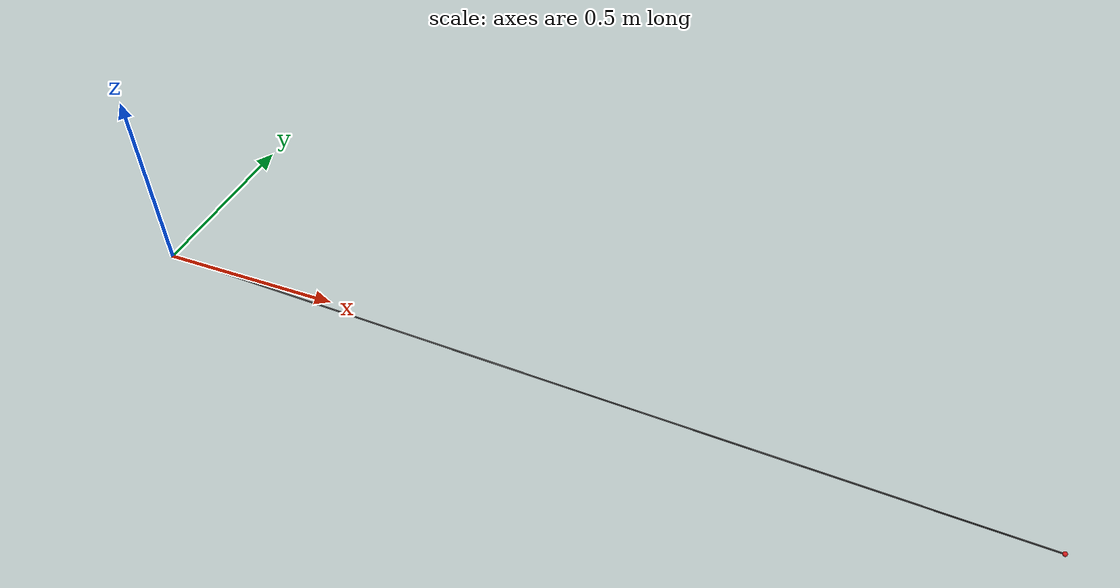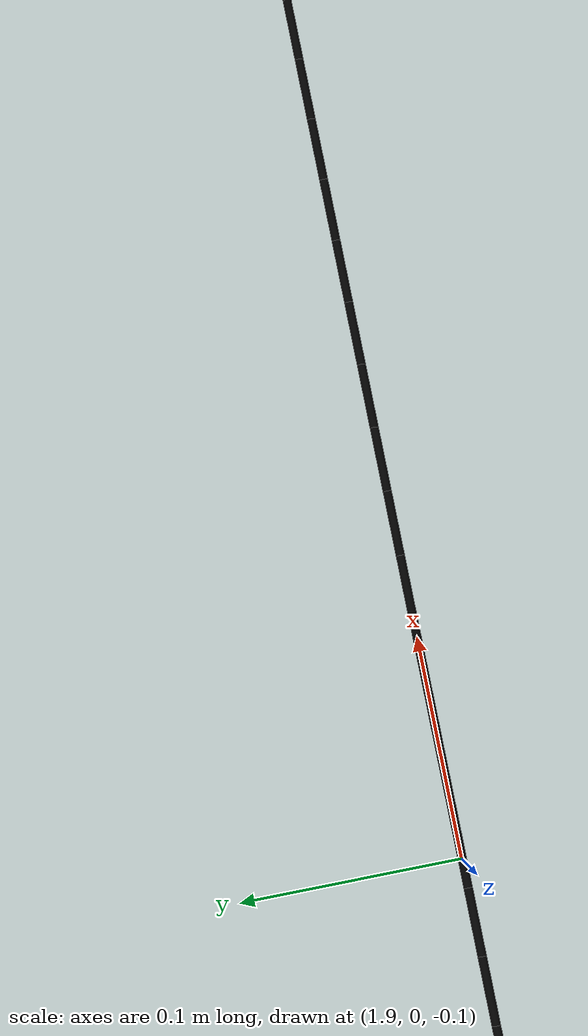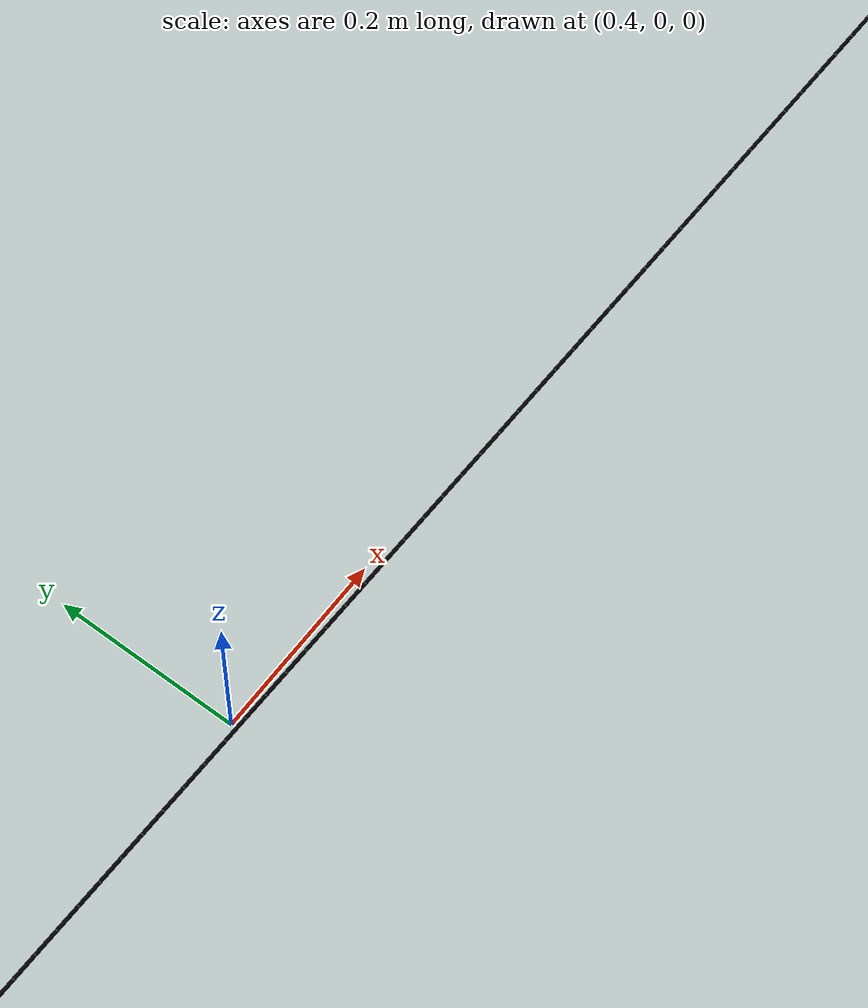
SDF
<?xml version="1.0" ?>
<sdf version="1.8">
  <model name="cabo_flexivel">
    <self_collide>false</self_collide>

    <plugin filename="gz-sim-joint-state-publisher-system" name="gz::sim::systems::JointStatePublisher"/>

    <link name="raiz_cabo">
      <pose>0 0 0 0 0 0</pose>
      <inertial>
        <mass>0.02</mass>
        <inertia>
          <ixx>1e-05</ixx><ixy>0</ixy><ixz>0</ixz>
          <iyy>1e-05</iyy><iyz>0</iyz><izz>1e-05</izz>
        </inertia>
      </inertial>
      <visual name="visual_raiz">
        <geometry><sphere><radius>0.005</radius></sphere></geometry>
        <material>
          <ambient>0.1 0.1 0.1 1</ambient>
          <diffuse>0.1 0.1 0.1 1</diffuse>
        </material>
      </visual>
    </link>

      <link name="segment_1">
        <pose>0.000000 0.000000 0.000000 0 0.050956 0.000000</pose>
        <enable_wind>false</enable_wind>
        <self_collide>false</self_collide>

        <visual name="visual">
          <pose>0.015000 0 0 0 1.5708 0</pose>
          <geometry><cylinder><radius>0.002</radius><length>0.030000</length></cylinder></geometry>
          <material>
            <ambient>0 0 0 1</ambient>
            <diffuse>0 0 0 1</diffuse>
          </material>
        </visual>
        <collision name="collision">
          <pose>0.015000 0 0 0 1.5708 0</pose>
          <geometry><cylinder><radius>0.001</radius><length>0.018000</length></cylinder></geometry>
        </collision>

        <inertial>
          <pose>0.015000 0 0 0 0 0</pose>
          <mass>0.0012000000000000003</mass>
          <inertia>
            <ixx>1e-05</ixx><ixy>0</ixy><ixz>0</ixz>
            <iyy>1e-05</iyy><iyz>0</iyz><izz>1e-05</izz>
          </inertia>
        </inertial>
      </link>

      <joint name="joint_1" type="universal">
        <parent>raiz_cabo</parent>
        <child>segment_1</child>
        <pose>0 0 0 0 0 0</pose>
        <axis>
          <xyz>0 1 0</xyz>
        <limit>
          <lower>-0.523599</lower>
          <upper>0.523599</upper>
        </limit>
        </axis>
        <axis2>
          <xyz>0 0 1</xyz>
        <limit>
          <lower>-0.523599</lower>
          <upper>0.523599</upper>
        </limit>
        </axis2>

      <dynamics>
        <damping>0.5</damping>
        <friction>0.1</friction>
      </dynamics>

      <sensor name="sensor_tensao_carretel" type="force_torque">
        <always_on>true</always_on>
        <update_rate>50</update_rate>
        <topic>/cabo/tensao_carretel</topic>
      </sensor>
      </joint>

      <link name="segment_2">
        <pose>0.029961 0.000000 -0.001528 0 0.050956 -0.000000</pose>
        <enable_wind>false</enable_wind>
        <self_collide>false</self_collide>

        <visual name="visual">
          <pose>0.015000 0 0 0 1.5708 0</pose>
          <geometry><cylinder><radius>0.002</radius><length>0.030000</length></cylinder></geometry>
          <material>
            <ambient>0 0 0 1</ambient>
            <diffuse>0 0 0 1</diffuse>
          </material>
        </visual>
        <collision name="collision">
          <pose>0.015000 0 0 0 1.5708 0</pose>
          <geometry><cylinder><radius>0.001</radius><length>0.018000</length></cylinder></geometry>
        </collision>

        <inertial>
          <pose>0.015000 0 0 0 0 0</pose>
          <mass>0.0011999999999999995</mass>
          <inertia>
            <ixx>1e-05</ixx><ixy>0</ixy><ixz>0</ixz>
            <iyy>1e-05</iyy><iyz>0</iyz><izz>1e-05</izz>
          </inertia>
        </inertial>
      </link>

      <joint name="joint_2" type="universal">
        <parent>segment_1</parent>
        <child>segment_2</child>
        <pose>0 0 0 0 0 0</pose>
        <axis>
          <xyz>0 1 0</xyz>
        <limit>
          <lower>-0.523599</lower>
          <upper>0.523599</upper>
        </limit>
        </axis>
        <axis2>
          <xyz>0 0 1</xyz>
        <limit>
          <lower>-0.523599</lower>
          <upper>0.523599</upper>
        </limit>
        </axis2>

      <dynamics>
        <damping>0.5</damping>
        <friction>0.1</friction>
      </dynamics>

      </joint>

      <link name="segment_3">
        <pose>0.059922 0.000000 -0.003056 0 0.050956 0.000000</pose>
        <enable_wind>false</enable_wind>
        <self_collide>false</self_collide>

        <visual name="visual">
          <pose>0.015000 0 0 0 1.5708 0</pose>
          <geometry><cylinder><radius>0.002</radius><length>0.030000</length></cylinder></geometry>
          <material>
            <ambient>0 0 0 1</ambient>
            <diffuse>0 0 0 1</diffuse>
          </material>
        </visual>
        <collision name="collision">
          <pose>0.015000 0 0 0 1.5708 0</pose>
          <geometry><cylinder><radius>0.001</radius><length>0.018000</length></cylinder></geometry>
        </collision>

        <inertial>
          <pose>0.015000 0 0 0 0 0</pose>
          <mass>0.0012000000000000014</mass>
          <inertia>
            <ixx>1e-05</ixx><ixy>0</ixy><ixz>0</ixz>
            <iyy>1e-05</iyy><iyz>0</iyz><izz>1e-05</izz>
          </inertia>
        </inertial>
      </link>

      <joint name="joint_3" type="universal">
        <parent>segment_2</parent>
        <child>segment_3</child>
        <pose>0 0 0 0 0 0</pose>
        <axis>
          <xyz>0 1 0</xyz>
        <limit>
          <lower>-0.523599</lower>
          <upper>0.523599</upper>
        </limit>
        </axis>
        <axis2>
          <xyz>0 0 1</xyz>
        <limit>
          <lower>-0.523599</lower>
          <upper>0.523599</upper>
        </limit>
        </axis2>

      <dynamics>
        <damping>0.5</damping>
        <friction>0.1</friction>
      </dynamics>

      </joint>

      <link name="segment_4">
        <pose>0.089883 0.000000 -0.004584 0 0.050956 -0.000000</pose>
        <enable_wind>false</enable_wind>
        <self_collide>false</self_collide>

        <visual name="visual">
          <pose>0.015000 0 0 0 1.5708 0</pose>
          <geometry><cylinder><radius>0.002</radius><length>0.030000</length></cylinder></geometry>
          <material>
            <ambient>0 0 0 1</ambient>
            <diffuse>0 0 0 1</diffuse>
          </material>
        </visual>
        <collision name="collision">
          <pose>0.015000 0 0 0 1.5708 0</pose>
          <geometry><cylinder><radius>0.001</radius><length>0.018000</length></cylinder></geometry>
        </collision>

        <inertial>
          <pose>0.015000 0 0 0 0 0</pose>
          <mass>0.0011999999999999988</mass>
          <inertia>
            <ixx>1e-05</ixx><ixy>0</ixy><ixz>0</ixz>
            <iyy>1e-05</iyy><iyz>0</iyz><izz>1e-05</izz>
          </inertia>
        </inertial>
      </link>

      <joint name="joint_4" type="universal">
        <parent>segment_3</parent>
        <child>segment_4</child>
        <pose>0 0 0 0 0 0</pose>
        <axis>
          <xyz>0 1 0</xyz>
        <limit>
          <lower>-0.523599</lower>
          <upper>0.523599</upper>
        </limit>
        </axis>
        <axis2>
          <xyz>0 0 1</xyz>
        <limit>
          <lower>-0.523599</lower>
          <upper>0.523599</upper>
        </limit>
        </axis2>

      <dynamics>
        <damping>0.5</damping>
        <friction>0.1</friction>
      </dynamics>

      </joint>

      <link name="segment_5">
        <pose>0.119844 0.000000 -0.006112 0 0.050956 0.000000</pose>
        <enable_wind>false</enable_wind>
        <self_collide>false</self_collide>

        <visual name="visual">
          <pose>0.015000 0 0 0 1.5708 0</pose>
          <geometry><cylinder><radius>0.002</radius><length>0.030000</length></cylinder></geometry>
          <material>
            <ambient>0 0 0 1</ambient>
            <diffuse>0 0 0 1</diffuse>
          </material>
        </visual>
        <collision name="collision">
          <pose>0.015000 0 0 0 1.5708 0</pose>
          <geometry><cylinder><radius>0.001</radius><length>0.018000</length></cylinder></geometry>
        </collision>

        <inertial>
          <pose>0.015000 0 0 0 0 0</pose>
          <mass>0.0012000000000000003</mass>
          <inertia>
            <ixx>1e-05</ixx><ixy>0</ixy><ixz>0</ixz>
            <iyy>1e-05</iyy><iyz>0</iyz><izz>1e-05</izz>
          </inertia>
        </inertial>
      </link>

      <joint name="joint_5" type="universal">
        <parent>segment_4</parent>
        <child>segment_5</child>
        <pose>0 0 0 0 0 0</pose>
        <axis>
          <xyz>0 1 0</xyz>
        <limit>
          <lower>-0.523599</lower>
          <upper>0.523599</upper>
        </limit>
        </axis>
        <axis2>
          <xyz>0 0 1</xyz>
        <limit>
          <lower>-0.523599</lower>
          <upper>0.523599</upper>
        </limit>
        </axis2>

      <dynamics>
        <damping>0.5</damping>
        <friction>0.1</friction>
      </dynamics>

      </joint>

      <link name="segment_6">
        <pose>0.149805 0.000000 -0.007640 0 0.050956 0.000000</pose>
        <enable_wind>false</enable_wind>
        <self_collide>false</self_collide>

        <visual name="visual">
          <pose>0.015000 0 0 0 1.5708 0</pose>
          <geometry><cylinder><radius>0.002</radius><length>0.030000</length></cylinder></geometry>
          <material>
            <ambient>0 0 0 1</ambient>
            <diffuse>0 0 0 1</diffuse>
          </material>
        </visual>
        <collision name="collision">
          <pose>0.015000 0 0 0 1.5708 0</pose>
          <geometry><cylinder><radius>0.001</radius><length>0.018000</length></cylinder></geometry>
        </collision>

        <inertial>
          <pose>0.015000 0 0 0 0 0</pose>
          <mass>0.0011999999999999878</mass>
          <inertia>
            <ixx>1e-05</ixx><ixy>0</ixy><ixz>0</ixz>
            <iyy>1e-05</iyy><iyz>0</iyz><izz>1e-05</izz>
          </inertia>
        </inertial>
      </link>

      <joint name="joint_6" type="universal">
        <parent>segment_5</parent>
        <child>segment_6</child>
        <pose>0 0 0 0 0 0</pose>
        <axis>
          <xyz>0 1 0</xyz>
        <limit>
          <lower>-0.523599</lower>
          <upper>0.523599</upper>
        </limit>
        </axis>
        <axis2>
          <xyz>0 0 1</xyz>
        <limit>
          <lower>-0.523599</lower>
          <upper>0.523599</upper>
        </limit>
        </axis2>

      <dynamics>
        <damping>0.5</damping>
        <friction>0.1</friction>
      </dynamics>

      </joint>

      <link name="segment_7">
        <pose>0.179766 0.000000 -0.009168 0 0.050956 -0.000000</pose>
        <enable_wind>false</enable_wind>
        <self_collide>false</self_collide>

        <visual name="visual">
          <pose>0.015000 0 0 0 1.5708 0</pose>
          <geometry><cylinder><radius>0.002</radius><length>0.030000</length></cylinder></geometry>
          <material>
            <ambient>0 0 0 1</ambient>
            <diffuse>0 0 0 1</diffuse>
          </material>
        </visual>
        <collision name="collision">
          <pose>0.015000 0 0 0 1.5708 0</pose>
          <geometry><cylinder><radius>0.001</radius><length>0.018000</length></cylinder></geometry>
        </collision>

        <inertial>
          <pose>0.015000 0 0 0 0 0</pose>
          <mass>0.0011999999999999914</mass>
          <inertia>
            <ixx>1e-05</ixx><ixy>0</ixy><ixz>0</ixz>
            <iyy>1e-05</iyy><iyz>0</iyz><izz>1e-05</izz>
          </inertia>
        </inertial>
      </link>

      <joint name="joint_7" type="universal">
        <parent>segment_6</parent>
        <child>segment_7</child>
        <pose>0 0 0 0 0 0</pose>
        <axis>
          <xyz>0 1 0</xyz>
        <limit>
          <lower>-0.523599</lower>
          <upper>0.523599</upper>
        </limit>
        </axis>
        <axis2>
          <xyz>0 0 1</xyz>
        <limit>
          <lower>-0.523599</lower>
          <upper>0.523599</upper>
        </limit>
        </axis2>

      <dynamics>
        <damping>0.5</damping>
        <friction>0.1</friction>
      </dynamics>

      </joint>

      <link name="segment_8">
        <pose>0.209727 -0.000000 -0.010696 0 0.050956 0.000000</pose>
        <enable_wind>false</enable_wind>
        <self_collide>false</self_collide>

        <visual name="visual">
          <pose>0.015000 0 0 0 1.5708 0</pose>
          <geometry><cylinder><radius>0.002</radius><length>0.030000</length></cylinder></geometry>
          <material>
            <ambient>0 0 0 1</ambient>
            <diffuse>0 0 0 1</diffuse>
          </material>
        </visual>
        <collision name="collision">
          <pose>0.015000 0 0 0 1.5708 0</pose>
          <geometry><cylinder><radius>0.001</radius><length>0.018000</length></cylinder></geometry>
        </collision>

        <inertial>
          <pose>0.015000 0 0 0 0 0</pose>
          <mass>0.0012000000000000014</mass>
          <inertia>
            <ixx>1e-05</ixx><ixy>0</ixy><ixz>0</ixz>
            <iyy>1e-05</iyy><iyz>0</iyz><izz>1e-05</izz>
          </inertia>
        </inertial>
      </link>

      <joint name="joint_8" type="universal">
        <parent>segment_7</parent>
        <child>segment_8</child>
        <pose>0 0 0 0 0 0</pose>
        <axis>
          <xyz>0 1 0</xyz>
        <limit>
          <lower>-0.523599</lower>
          <upper>0.523599</upper>
        </limit>
        </axis>
        <axis2>
          <xyz>0 0 1</xyz>
        <limit>
          <lower>-0.523599</lower>
          <upper>0.523599</upper>
        </limit>
        </axis2>

      <dynamics>
        <damping>0.5</damping>
        <friction>0.1</friction>
      </dynamics>

      </joint>

      <link name="segment_9">
        <pose>0.239688 0.000000 -0.012224 0 0.050956 0.000000</pose>
        <enable_wind>false</enable_wind>
        <self_collide>false</self_collide>

        <visual name="visual">
          <pose>0.015000 0 0 0 1.5708 0</pose>
          <geometry><cylinder><radius>0.002</radius><length>0.030000</length></cylinder></geometry>
          <material>
            <ambient>0 0 0 1</ambient>
            <diffuse>0 0 0 1</diffuse>
          </material>
        </visual>
        <collision name="collision">
          <pose>0.015000 0 0 0 1.5708 0</pose>
          <geometry><cylinder><radius>0.001</radius><length>0.018000</length></cylinder></geometry>
        </collision>

        <inertial>
          <pose>0.015000 0 0 0 0 0</pose>
          <mass>0.0011999999999999958</mass>
          <inertia>
            <ixx>1e-05</ixx><ixy>0</ixy><ixz>0</ixz>
            <iyy>1e-05</iyy><iyz>0</iyz><izz>1e-05</izz>
          </inertia>
        </inertial>
      </link>

      <joint name="joint_9" type="universal">
        <parent>segment_8</parent>
        <child>segment_9</child>
        <pose>0 0 0 0 0 0</pose>
        <axis>
          <xyz>0 1 0</xyz>
        <limit>
          <lower>-0.523599</lower>
          <upper>0.523599</upper>
        </limit>
        </axis>
        <axis2>
          <xyz>0 0 1</xyz>
        <limit>
          <lower>-0.523599</lower>
          <upper>0.523599</upper>
        </limit>
        </axis2>

      <dynamics>
        <damping>0.5</damping>
        <friction>0.1</friction>
      </dynamics>

      </joint>

      <link name="segment_10">
        <pose>0.269650 0.000000 -0.013752 0 0.050956 -0.000000</pose>
        <enable_wind>false</enable_wind>
        <self_collide>false</self_collide>

        <visual name="visual">
          <pose>0.015000 0 0 0 1.5708 0</pose>
          <geometry><cylinder><radius>0.002</radius><length>0.030000</length></cylinder></geometry>
          <material>
            <ambient>0 0 0 1</ambient>
            <diffuse>0 0 0 1</diffuse>
          </material>
        </visual>
        <collision name="collision">
          <pose>0.015000 0 0 0 1.5708 0</pose>
          <geometry><cylinder><radius>0.001</radius><length>0.018000</length></cylinder></geometry>
        </collision>

        <inertial>
          <pose>0.015000 0 0 0 0 0</pose>
          <mass>0.0012000000000000034</mass>
          <inertia>
            <ixx>1e-05</ixx><ixy>0</ixy><ixz>0</ixz>
            <iyy>1e-05</iyy><iyz>0</iyz><izz>1e-05</izz>
          </inertia>
        </inertial>
      </link>

      <joint name="joint_10" type="universal">
        <parent>segment_9</parent>
        <child>segment_10</child>
        <pose>0 0 0 0 0 0</pose>
        <axis>
          <xyz>0 1 0</xyz>
        <limit>
          <lower>-0.523599</lower>
          <upper>0.523599</upper>
        </limit>
        </axis>
        <axis2>
          <xyz>0 0 1</xyz>
        <limit>
          <lower>-0.523599</lower>
          <upper>0.523599</upper>
        </limit>
        </axis2>

      <dynamics>
        <damping>0.5</damping>
        <friction>0.1</friction>
      </dynamics>

      </joint>

      <link name="segment_11">
        <pose>0.299611 -0.000000 -0.015280 0 0.050956 0.000000</pose>
        <enable_wind>false</enable_wind>
        <self_collide>false</self_collide>

        <visual name="visual">
          <pose>0.015000 0 0 0 1.5708 0</pose>
          <geometry><cylinder><radius>0.002</radius><length>0.030000</length></cylinder></geometry>
          <material>
            <ambient>0 0 0 1</ambient>
            <diffuse>0 0 0 1</diffuse>
          </material>
        </visual>
        <collision name="collision">
          <pose>0.015000 0 0 0 1.5708 0</pose>
          <geometry><cylinder><radius>0.001</radius><length>0.018000</length></cylinder></geometry>
        </collision>

        <inertial>
          <pose>0.015000 0 0 0 0 0</pose>
          <mass>0.001199999999999997</mass>
          <inertia>
            <ixx>1e-05</ixx><ixy>0</ixy><ixz>0</ixz>
            <iyy>1e-05</iyy><iyz>0</iyz><izz>1e-05</izz>
          </inertia>
        </inertial>
      </link>

      <joint name="joint_11" type="universal">
        <parent>segment_10</parent>
        <child>segment_11</child>
        <pose>0 0 0 0 0 0</pose>
        <axis>
          <xyz>0 1 0</xyz>
        <limit>
          <lower>-0.523599</lower>
          <upper>0.523599</upper>
        </limit>
        </axis>
        <axis2>
          <xyz>0 0 1</xyz>
        <limit>
          <lower>-0.523599</lower>
          <upper>0.523599</upper>
        </limit>
        </axis2>

      <dynamics>
        <damping>0.5</damping>
        <friction>0.1</friction>
      </dynamics>

      </joint>

      <link name="segment_12">
        <pose>0.329572 -0.000000 -0.016808 0 0.050956 0.000000</pose>
        <enable_wind>false</enable_wind>
        <self_collide>false</self_collide>

        <visual name="visual">
          <pose>0.015000 0 0 0 1.5708 0</pose>
          <geometry><cylinder><radius>0.002</radius><length>0.030000</length></cylinder></geometry>
          <material>
            <ambient>0 0 0 1</ambient>
            <diffuse>0 0 0 1</diffuse>
          </material>
        </visual>
        <collision name="collision">
          <pose>0.015000 0 0 0 1.5708 0</pose>
          <geometry><cylinder><radius>0.001</radius><length>0.018000</length></cylinder></geometry>
        </collision>

        <inertial>
          <pose>0.015000 0 0 0 0 0</pose>
          <mass>0.0012000000000000012</mass>
          <inertia>
            <ixx>1e-05</ixx><ixy>0</ixy><ixz>0</ixz>
            <iyy>1e-05</iyy><iyz>0</iyz><izz>1e-05</izz>
          </inertia>
        </inertial>
      </link>

      <joint name="joint_12" type="universal">
        <parent>segment_11</parent>
        <child>segment_12</child>
        <pose>0 0 0 0 0 0</pose>
        <axis>
          <xyz>0 1 0</xyz>
        <limit>
          <lower>-0.523599</lower>
          <upper>0.523599</upper>
        </limit>
        </axis>
        <axis2>
          <xyz>0 0 1</xyz>
        <limit>
          <lower>-0.523599</lower>
          <upper>0.523599</upper>
        </limit>
        </axis2>

      <dynamics>
        <damping>0.5</damping>
        <friction>0.1</friction>
      </dynamics>

      </joint>

      <link name="segment_13">
        <pose>0.359533 0.000000 -0.018336 0 0.050956 0.000000</pose>
        <enable_wind>false</enable_wind>
        <self_collide>false</self_collide>

        <visual name="visual">
          <pose>0.015000 0 0 0 1.5708 0</pose>
          <geometry><cylinder><radius>0.002</radius><length>0.030000</length></cylinder></geometry>
          <material>
            <ambient>0 0 0 1</ambient>
            <diffuse>0 0 0 1</diffuse>
          </material>
        </visual>
        <collision name="collision">
          <pose>0.015000 0 0 0 1.5708 0</pose>
          <geometry><cylinder><radius>0.001</radius><length>0.018000</length></cylinder></geometry>
        </collision>

        <inertial>
          <pose>0.015000 0 0 0 0 0</pose>
          <mass>0.0012000000000000014</mass>
          <inertia>
            <ixx>1e-05</ixx><ixy>0</ixy><ixz>0</ixz>
            <iyy>1e-05</iyy><iyz>0</iyz><izz>1e-05</izz>
          </inertia>
        </inertial>
      </link>

      <joint name="joint_13" type="universal">
        <parent>segment_12</parent>
        <child>segment_13</child>
        <pose>0 0 0 0 0 0</pose>
        <axis>
          <xyz>0 1 0</xyz>
        <limit>
          <lower>-0.523599</lower>
          <upper>0.523599</upper>
        </limit>
        </axis>
        <axis2>
          <xyz>0 0 1</xyz>
        <limit>
          <lower>-0.523599</lower>
          <upper>0.523599</upper>
        </limit>
        </axis2>

      <dynamics>
        <damping>0.5</damping>
        <friction>0.1</friction>
      </dynamics>

      </joint>

      <link name="segment_14">
        <pose>0.389494 0.000000 -0.019864 0 0.050956 0.000000</pose>
        <enable_wind>false</enable_wind>
        <self_collide>false</self_collide>

        <visual name="visual">
          <pose>0.015000 0 0 0 1.5708 0</pose>
          <geometry><cylinder><radius>0.002</radius><length>0.030000</length></cylinder></geometry>
          <material>
            <ambient>0 0 0 1</ambient>
            <diffuse>0 0 0 1</diffuse>
          </material>
        </visual>
        <collision name="collision">
          <pose>0.015000 0 0 0 1.5708 0</pose>
          <geometry><cylinder><radius>0.001</radius><length>0.018000</length></cylinder></geometry>
        </collision>

        <inertial>
          <pose>0.015000 0 0 0 0 0</pose>
          <mass>0.0011999999999999945</mass>
          <inertia>
            <ixx>1e-05</ixx><ixy>0</ixy><ixz>0</ixz>
            <iyy>1e-05</iyy><iyz>0</iyz><izz>1e-05</izz>
          </inertia>
        </inertial>
      </link>

      <joint name="joint_14" type="universal">
        <parent>segment_13</parent>
        <child>segment_14</child>
        <pose>0 0 0 0 0 0</pose>
        <axis>
          <xyz>0 1 0</xyz>
        <limit>
          <lower>-0.523599</lower>
          <upper>0.523599</upper>
        </limit>
        </axis>
        <axis2>
          <xyz>0 0 1</xyz>
        <limit>
          <lower>-0.523599</lower>
          <upper>0.523599</upper>
        </limit>
        </axis2>

      <dynamics>
        <damping>0.5</damping>
        <friction>0.1</friction>
      </dynamics>

      </joint>

      <link name="segment_15">
        <pose>0.419455 0.000000 -0.021392 0 0.050956 0.000000</pose>
        <enable_wind>false</enable_wind>
        <self_collide>false</self_collide>

        <visual name="visual">
          <pose>0.015000 0 0 0 1.5708 0</pose>
          <geometry><cylinder><radius>0.002</radius><length>0.030000</length></cylinder></geometry>
          <material>
            <ambient>0 0 0 1</ambient>
            <diffuse>0 0 0 1</diffuse>
          </material>
        </visual>
        <collision name="collision">
          <pose>0.015000 0 0 0 1.5708 0</pose>
          <geometry><cylinder><radius>0.001</radius><length>0.018000</length></cylinder></geometry>
        </collision>

        <inertial>
          <pose>0.015000 0 0 0 0 0</pose>
          <mass>0.0011999999999999969</mass>
          <inertia>
            <ixx>1e-05</ixx><ixy>0</ixy><ixz>0</ixz>
            <iyy>1e-05</iyy><iyz>0</iyz><izz>1e-05</izz>
          </inertia>
        </inertial>
      </link>

      <joint name="joint_15" type="universal">
        <parent>segment_14</parent>
        <child>segment_15</child>
        <pose>0 0 0 0 0 0</pose>
        <axis>
          <xyz>0 1 0</xyz>
        <limit>
          <lower>-0.523599</lower>
          <upper>0.523599</upper>
        </limit>
        </axis>
        <axis2>
          <xyz>0 0 1</xyz>
        <limit>
          <lower>-0.523599</lower>
          <upper>0.523599</upper>
        </limit>
        </axis2>

      <dynamics>
        <damping>0.5</damping>
        <friction>0.1</friction>
      </dynamics>

      </joint>

      <link name="segment_16">
        <pose>0.449416 0.000000 -0.022920 0 0.050956 0.000000</pose>
        <enable_wind>false</enable_wind>
        <self_collide>false</self_collide>

        <visual name="visual">
          <pose>0.015000 0 0 0 1.5708 0</pose>
          <geometry><cylinder><radius>0.002</radius><length>0.030000</length></cylinder></geometry>
          <material>
            <ambient>0 0 0 1</ambient>
            <diffuse>0 0 0 1</diffuse>
          </material>
        </visual>
        <collision name="collision">
          <pose>0.015000 0 0 0 1.5708 0</pose>
          <geometry><cylinder><radius>0.001</radius><length>0.018000</length></cylinder></geometry>
        </collision>

        <inertial>
          <pose>0.015000 0 0 0 0 0</pose>
          <mass>0.0012000000000000014</mass>
          <inertia>
            <ixx>1e-05</ixx><ixy>0</ixy><ixz>0</ixz>
            <iyy>1e-05</iyy><iyz>0</iyz><izz>1e-05</izz>
          </inertia>
        </inertial>
      </link>

      <joint name="joint_16" type="universal">
        <parent>segment_15</parent>
        <child>segment_16</child>
        <pose>0 0 0 0 0 0</pose>
        <axis>
          <xyz>0 1 0</xyz>
        <limit>
          <lower>-0.523599</lower>
          <upper>0.523599</upper>
        </limit>
        </axis>
        <axis2>
          <xyz>0 0 1</xyz>
        <limit>
          <lower>-0.523599</lower>
          <upper>0.523599</upper>
        </limit>
        </axis2>

      <dynamics>
        <damping>0.5</damping>
        <friction>0.1</friction>
      </dynamics>

      </joint>

      <link name="segment_17">
        <pose>0.479377 0.000000 -0.024448 0 0.050956 -0.000000</pose>
        <enable_wind>false</enable_wind>
        <self_collide>false</self_collide>

        <visual name="visual">
          <pose>0.015000 0 0 0 1.5708 0</pose>
          <geometry><cylinder><radius>0.002</radius><length>0.030000</length></cylinder></geometry>
          <material>
            <ambient>0 0 0 1</ambient>
            <diffuse>0 0 0 1</diffuse>
          </material>
        </visual>
        <collision name="collision">
          <pose>0.015000 0 0 0 1.5708 0</pose>
          <geometry><cylinder><radius>0.001</radius><length>0.018000</length></cylinder></geometry>
        </collision>

        <inertial>
          <pose>0.015000 0 0 0 0 0</pose>
          <mass>0.0012000000000000081</mass>
          <inertia>
            <ixx>1e-05</ixx><ixy>0</ixy><ixz>0</ixz>
            <iyy>1e-05</iyy><iyz>0</iyz><izz>1e-05</izz>
          </inertia>
        </inertial>
      </link>

      <joint name="joint_17" type="universal">
        <parent>segment_16</parent>
        <child>segment_17</child>
        <pose>0 0 0 0 0 0</pose>
        <axis>
          <xyz>0 1 0</xyz>
        <limit>
          <lower>-0.523599</lower>
          <upper>0.523599</upper>
        </limit>
        </axis>
        <axis2>
          <xyz>0 0 1</xyz>
        <limit>
          <lower>-0.523599</lower>
          <upper>0.523599</upper>
        </limit>
        </axis2>

      <dynamics>
        <damping>0.5</damping>
        <friction>0.1</friction>
      </dynamics>

      </joint>

      <link name="segment_18">
        <pose>0.509338 -0.000000 -0.025976 0 0.050956 0.000000</pose>
        <enable_wind>false</enable_wind>
        <self_collide>false</self_collide>

        <visual name="visual">
          <pose>0.015000 0 0 0 1.5708 0</pose>
          <geometry><cylinder><radius>0.002</radius><length>0.030000</length></cylinder></geometry>
          <material>
            <ambient>0 0 0 1</ambient>
            <diffuse>0 0 0 1</diffuse>
          </material>
        </visual>
        <collision name="collision">
          <pose>0.015000 0 0 0 1.5708 0</pose>
          <geometry><cylinder><radius>0.001</radius><length>0.018000</length></cylinder></geometry>
        </collision>

        <inertial>
          <pose>0.015000 0 0 0 0 0</pose>
          <mass>0.0011999999999999815</mass>
          <inertia>
            <ixx>1e-05</ixx><ixy>0</ixy><ixz>0</ixz>
            <iyy>1e-05</iyy><iyz>0</iyz><izz>1e-05</izz>
          </inertia>
        </inertial>
      </link>

      <joint name="joint_18" type="universal">
        <parent>segment_17</parent>
        <child>segment_18</child>
        <pose>0 0 0 0 0 0</pose>
        <axis>
          <xyz>0 1 0</xyz>
        <limit>
          <lower>-0.523599</lower>
          <upper>0.523599</upper>
        </limit>
        </axis>
        <axis2>
          <xyz>0 0 1</xyz>
        <limit>
          <lower>-0.523599</lower>
          <upper>0.523599</upper>
        </limit>
        </axis2>

      <dynamics>
        <damping>0.5</damping>
        <friction>0.1</friction>
      </dynamics>

      </joint>

      <link name="segment_19">
        <pose>0.539299 -0.000000 -0.027504 0 0.050956 0.000000</pose>
        <enable_wind>false</enable_wind>
        <self_collide>false</self_collide>

        <visual name="visual">
          <pose>0.015000 0 0 0 1.5708 0</pose>
          <geometry><cylinder><radius>0.002</radius><length>0.030000</length></cylinder></geometry>
          <material>
            <ambient>0 0 0 1</ambient>
            <diffuse>0 0 0 1</diffuse>
          </material>
        </visual>
        <collision name="collision">
          <pose>0.015000 0 0 0 1.5708 0</pose>
          <geometry><cylinder><radius>0.001</radius><length>0.018000</length></cylinder></geometry>
        </collision>

        <inertial>
          <pose>0.015000 0 0 0 0 0</pose>
          <mass>0.0011999999999999856</mass>
          <inertia>
            <ixx>1e-05</ixx><ixy>0</ixy><ixz>0</ixz>
            <iyy>1e-05</iyy><iyz>0</iyz><izz>1e-05</izz>
          </inertia>
        </inertial>
      </link>

      <joint name="joint_19" type="universal">
        <parent>segment_18</parent>
        <child>segment_19</child>
        <pose>0 0 0 0 0 0</pose>
        <axis>
          <xyz>0 1 0</xyz>
        <limit>
          <lower>-0.523599</lower>
          <upper>0.523599</upper>
        </limit>
        </axis>
        <axis2>
          <xyz>0 0 1</xyz>
        <limit>
          <lower>-0.523599</lower>
          <upper>0.523599</upper>
        </limit>
        </axis2>

      <dynamics>
        <damping>0.5</damping>
        <friction>0.1</friction>
      </dynamics>

      </joint>

      <link name="segment_20">
        <pose>0.569260 -0.000000 -0.029032 0 0.050956 0.000000</pose>
        <enable_wind>false</enable_wind>
        <self_collide>false</self_collide>

        <visual name="visual">
          <pose>0.015000 0 0 0 1.5708 0</pose>
          <geometry><cylinder><radius>0.002</radius><length>0.030000</length></cylinder></geometry>
          <material>
            <ambient>0 0 0 1</ambient>
            <diffuse>0 0 0 1</diffuse>
          </material>
        </visual>
        <collision name="collision">
          <pose>0.015000 0 0 0 1.5708 0</pose>
          <geometry><cylinder><radius>0.001</radius><length>0.018000</length></cylinder></geometry>
        </collision>

        <inertial>
          <pose>0.015000 0 0 0 0 0</pose>
          <mass>0.0011999999999999591</mass>
          <inertia>
            <ixx>1e-05</ixx><ixy>0</ixy><ixz>0</ixz>
            <iyy>1e-05</iyy><iyz>0</iyz><izz>1e-05</izz>
          </inertia>
        </inertial>
      </link>

      <joint name="joint_20" type="universal">
        <parent>segment_19</parent>
        <child>segment_20</child>
        <pose>0 0 0 0 0 0</pose>
        <axis>
          <xyz>0 1 0</xyz>
        <limit>
          <lower>-0.523599</lower>
          <upper>0.523599</upper>
        </limit>
        </axis>
        <axis2>
          <xyz>0 0 1</xyz>
        <limit>
          <lower>-0.523599</lower>
          <upper>0.523599</upper>
        </limit>
        </axis2>

      <dynamics>
        <damping>0.5</damping>
        <friction>0.1</friction>
      </dynamics>

      </joint>

      <link name="segment_21">
        <pose>0.599221 0.000000 -0.030560 0 0.050956 -0.000000</pose>
        <enable_wind>false</enable_wind>
        <self_collide>false</self_collide>

        <visual name="visual">
          <pose>0.015000 0 0 0 1.5708 0</pose>
          <geometry><cylinder><radius>0.002</radius><length>0.030000</length></cylinder></geometry>
          <material>
            <ambient>0 0 0 1</ambient>
            <diffuse>0 0 0 1</diffuse>
          </material>
        </visual>
        <collision name="collision">
          <pose>0.015000 0 0 0 1.5708 0</pose>
          <geometry><cylinder><radius>0.001</radius><length>0.018000</length></cylinder></geometry>
        </collision>

        <inertial>
          <pose>0.015000 0 0 0 0 0</pose>
          <mass>0.0012000000000000125</mass>
          <inertia>
            <ixx>1e-05</ixx><ixy>0</ixy><ixz>0</ixz>
            <iyy>1e-05</iyy><iyz>0</iyz><izz>1e-05</izz>
          </inertia>
        </inertial>
      </link>

      <joint name="joint_21" type="universal">
        <parent>segment_20</parent>
        <child>segment_21</child>
        <pose>0 0 0 0 0 0</pose>
        <axis>
          <xyz>0 1 0</xyz>
        <limit>
          <lower>-0.523599</lower>
          <upper>0.523599</upper>
        </limit>
        </axis>
        <axis2>
          <xyz>0 0 1</xyz>
        <limit>
          <lower>-0.523599</lower>
          <upper>0.523599</upper>
        </limit>
        </axis2>

      <dynamics>
        <damping>0.5</damping>
        <friction>0.1</friction>
      </dynamics>

      </joint>

      <link name="segment_22">
        <pose>0.629182 -0.000000 -0.032088 0 0.050956 0.000000</pose>
        <enable_wind>false</enable_wind>
        <self_collide>false</self_collide>

        <visual name="visual">
          <pose>0.015000 0 0 0 1.5708 0</pose>
          <geometry><cylinder><radius>0.002</radius><length>0.030000</length></cylinder></geometry>
          <material>
            <ambient>0 0 0 1</ambient>
            <diffuse>0 0 0 1</diffuse>
          </material>
        </visual>
        <collision name="collision">
          <pose>0.015000 0 0 0 1.5708 0</pose>
          <geometry><cylinder><radius>0.001</radius><length>0.018000</length></cylinder></geometry>
        </collision>

        <inertial>
          <pose>0.015000 0 0 0 0 0</pose>
          <mass>0.0011999999999999856</mass>
          <inertia>
            <ixx>1e-05</ixx><ixy>0</ixy><ixz>0</ixz>
            <iyy>1e-05</iyy><iyz>0</iyz><izz>1e-05</izz>
          </inertia>
        </inertial>
      </link>

      <joint name="joint_22" type="universal">
        <parent>segment_21</parent>
        <child>segment_22</child>
        <pose>0 0 0 0 0 0</pose>
        <axis>
          <xyz>0 1 0</xyz>
        <limit>
          <lower>-0.523599</lower>
          <upper>0.523599</upper>
        </limit>
        </axis>
        <axis2>
          <xyz>0 0 1</xyz>
        <limit>
          <lower>-0.523599</lower>
          <upper>0.523599</upper>
        </limit>
        </axis2>

      <dynamics>
        <damping>0.5</damping>
        <friction>0.1</friction>
      </dynamics>

      </joint>

      <link name="segment_23">
        <pose>0.659143 0.000000 -0.033616 0 0.050956 0.000000</pose>
        <enable_wind>false</enable_wind>
        <self_collide>false</self_collide>

        <visual name="visual">
          <pose>0.015000 0 0 0 1.5708 0</pose>
          <geometry><cylinder><radius>0.002</radius><length>0.030000</length></cylinder></geometry>
          <material>
            <ambient>0 0 0 1</ambient>
            <diffuse>0 0 0 1</diffuse>
          </material>
        </visual>
        <collision name="collision">
          <pose>0.015000 0 0 0 1.5708 0</pose>
          <geometry><cylinder><radius>0.001</radius><length>0.018000</length></cylinder></geometry>
        </collision>

        <inertial>
          <pose>0.015000 0 0 0 0 0</pose>
          <mass>0.0011999999999999812</mass>
          <inertia>
            <ixx>1e-05</ixx><ixy>0</ixy><ixz>0</ixz>
            <iyy>1e-05</iyy><iyz>0</iyz><izz>1e-05</izz>
          </inertia>
        </inertial>
      </link>

      <joint name="joint_23" type="universal">
        <parent>segment_22</parent>
        <child>segment_23</child>
        <pose>0 0 0 0 0 0</pose>
        <axis>
          <xyz>0 1 0</xyz>
        <limit>
          <lower>-0.523599</lower>
          <upper>0.523599</upper>
        </limit>
        </axis>
        <axis2>
          <xyz>0 0 1</xyz>
        <limit>
          <lower>-0.523599</lower>
          <upper>0.523599</upper>
        </limit>
        </axis2>

      <dynamics>
        <damping>0.5</damping>
        <friction>0.1</friction>
      </dynamics>

      </joint>

      <link name="segment_24">
        <pose>0.689104 0.000000 -0.035144 0 0.050956 0.000000</pose>
        <enable_wind>false</enable_wind>
        <self_collide>false</self_collide>

        <visual name="visual">
          <pose>0.015000 0 0 0 1.5708 0</pose>
          <geometry><cylinder><radius>0.002</radius><length>0.030000</length></cylinder></geometry>
          <material>
            <ambient>0 0 0 1</ambient>
            <diffuse>0 0 0 1</diffuse>
          </material>
        </visual>
        <collision name="collision">
          <pose>0.015000 0 0 0 1.5708 0</pose>
          <geometry><cylinder><radius>0.001</radius><length>0.018000</length></cylinder></geometry>
        </collision>

        <inertial>
          <pose>0.015000 0 0 0 0 0</pose>
          <mass>0.0012000000000000081</mass>
          <inertia>
            <ixx>1e-05</ixx><ixy>0</ixy><ixz>0</ixz>
            <iyy>1e-05</iyy><iyz>0</iyz><izz>1e-05</izz>
          </inertia>
        </inertial>
      </link>

      <joint name="joint_24" type="universal">
        <parent>segment_23</parent>
        <child>segment_24</child>
        <pose>0 0 0 0 0 0</pose>
        <axis>
          <xyz>0 1 0</xyz>
        <limit>
          <lower>-0.523599</lower>
          <upper>0.523599</upper>
        </limit>
        </axis>
        <axis2>
          <xyz>0 0 1</xyz>
        <limit>
          <lower>-0.523599</lower>
          <upper>0.523599</upper>
        </limit>
        </axis2>

      <dynamics>
        <damping>0.5</damping>
        <friction>0.1</friction>
      </dynamics>

      </joint>

      <link name="segment_25">
        <pose>0.719065 0.000000 -0.036672 0 0.050956 0.000000</pose>
        <enable_wind>false</enable_wind>
        <self_collide>false</self_collide>

        <visual name="visual">
          <pose>0.015000 0 0 0 1.5708 0</pose>
          <geometry><cylinder><radius>0.002</radius><length>0.030000</length></cylinder></geometry>
          <material>
            <ambient>0 0 0 1</ambient>
            <diffuse>0 0 0 1</diffuse>
          </material>
        </visual>
        <collision name="collision">
          <pose>0.015000 0 0 0 1.5708 0</pose>
          <geometry><cylinder><radius>0.001</radius><length>0.018000</length></cylinder></geometry>
        </collision>

        <inertial>
          <pose>0.015000 0 0 0 0 0</pose>
          <mass>0.0012000000000000346</mass>
          <inertia>
            <ixx>1e-05</ixx><ixy>0</ixy><ixz>0</ixz>
            <iyy>1e-05</iyy><iyz>0</iyz><izz>1e-05</izz>
          </inertia>
        </inertial>
      </link>

      <joint name="joint_25" type="universal">
        <parent>segment_24</parent>
        <child>segment_25</child>
        <pose>0 0 0 0 0 0</pose>
        <axis>
          <xyz>0 1 0</xyz>
        <limit>
          <lower>-0.523599</lower>
          <upper>0.523599</upper>
        </limit>
        </axis>
        <axis2>
          <xyz>0 0 1</xyz>
        <limit>
          <lower>-0.523599</lower>
          <upper>0.523599</upper>
        </limit>
        </axis2>

      <dynamics>
        <damping>0.5</damping>
        <friction>0.1</friction>
      </dynamics>

      </joint>

      <link name="segment_26">
        <pose>0.749027 0.000000 -0.038200 0 0.050956 0.000000</pose>
        <enable_wind>false</enable_wind>
        <self_collide>false</self_collide>

        <visual name="visual">
          <pose>0.015000 0 0 0 1.5708 0</pose>
          <geometry><cylinder><radius>0.002</radius><length>0.030000</length></cylinder></geometry>
          <material>
            <ambient>0 0 0 1</ambient>
            <diffuse>0 0 0 1</diffuse>
          </material>
        </visual>
        <collision name="collision">
          <pose>0.015000 0 0 0 1.5708 0</pose>
          <geometry><cylinder><radius>0.001</radius><length>0.018000</length></cylinder></geometry>
        </collision>

        <inertial>
          <pose>0.015000 0 0 0 0 0</pose>
          <mass>0.001199999999999977</mass>
          <inertia>
            <ixx>1e-05</ixx><ixy>0</ixy><ixz>0</ixz>
            <iyy>1e-05</iyy><iyz>0</iyz><izz>1e-05</izz>
          </inertia>
        </inertial>
      </link>

      <joint name="joint_26" type="universal">
        <parent>segment_25</parent>
        <child>segment_26</child>
        <pose>0 0 0 0 0 0</pose>
        <axis>
          <xyz>0 1 0</xyz>
        <limit>
          <lower>-0.523599</lower>
          <upper>0.523599</upper>
        </limit>
        </axis>
        <axis2>
          <xyz>0 0 1</xyz>
        <limit>
          <lower>-0.523599</lower>
          <upper>0.523599</upper>
        </limit>
        </axis2>

      <dynamics>
        <damping>0.5</damping>
        <friction>0.1</friction>
      </dynamics>

      </joint>

      <link name="segment_27">
        <pose>0.778988 0.000000 -0.039728 0 0.050956 -0.000000</pose>
        <enable_wind>false</enable_wind>
        <self_collide>false</self_collide>

        <visual name="visual">
          <pose>0.015000 0 0 0 1.5708 0</pose>
          <geometry><cylinder><radius>0.002</radius><length>0.030000</length></cylinder></geometry>
          <material>
            <ambient>0 0 0 1</ambient>
            <diffuse>0 0 0 1</diffuse>
          </material>
        </visual>
        <collision name="collision">
          <pose>0.015000 0 0 0 1.5708 0</pose>
          <geometry><cylinder><radius>0.001</radius><length>0.018000</length></cylinder></geometry>
        </collision>

        <inertial>
          <pose>0.015000 0 0 0 0 0</pose>
          <mass>0.0012000000000000216</mass>
          <inertia>
            <ixx>1e-05</ixx><ixy>0</ixy><ixz>0</ixz>
            <iyy>1e-05</iyy><iyz>0</iyz><izz>1e-05</izz>
          </inertia>
        </inertial>
      </link>

      <joint name="joint_27" type="universal">
        <parent>segment_26</parent>
        <child>segment_27</child>
        <pose>0 0 0 0 0 0</pose>
        <axis>
          <xyz>0 1 0</xyz>
        <limit>
          <lower>-0.523599</lower>
          <upper>0.523599</upper>
        </limit>
        </axis>
        <axis2>
          <xyz>0 0 1</xyz>
        <limit>
          <lower>-0.523599</lower>
          <upper>0.523599</upper>
        </limit>
        </axis2>

      <dynamics>
        <damping>0.5</damping>
        <friction>0.1</friction>
      </dynamics>

      </joint>

      <link name="segment_28">
        <pose>0.808949 0.000000 -0.041256 0 0.050956 -0.000000</pose>
        <enable_wind>false</enable_wind>
        <self_collide>false</self_collide>

        <visual name="visual">
          <pose>0.015000 0 0 0 1.5708 0</pose>
          <geometry><cylinder><radius>0.002</radius><length>0.030000</length></cylinder></geometry>
          <material>
            <ambient>0 0 0 1</ambient>
            <diffuse>0 0 0 1</diffuse>
          </material>
        </visual>
        <collision name="collision">
          <pose>0.015000 0 0 0 1.5708 0</pose>
          <geometry><cylinder><radius>0.001</radius><length>0.018000</length></cylinder></geometry>
        </collision>

        <inertial>
          <pose>0.015000 0 0 0 0 0</pose>
          <mass>0.0012000000000000214</mass>
          <inertia>
            <ixx>1e-05</ixx><ixy>0</ixy><ixz>0</ixz>
            <iyy>1e-05</iyy><iyz>0</iyz><izz>1e-05</izz>
          </inertia>
        </inertial>
      </link>

      <joint name="joint_28" type="universal">
        <parent>segment_27</parent>
        <child>segment_28</child>
        <pose>0 0 0 0 0 0</pose>
        <axis>
          <xyz>0 1 0</xyz>
        <limit>
          <lower>-0.523599</lower>
          <upper>0.523599</upper>
        </limit>
        </axis>
        <axis2>
          <xyz>0 0 1</xyz>
        <limit>
          <lower>-0.523599</lower>
          <upper>0.523599</upper>
        </limit>
        </axis2>

      <dynamics>
        <damping>0.5</damping>
        <friction>0.1</friction>
      </dynamics>

      </joint>

      <link name="segment_29">
        <pose>0.838910 -0.000000 -0.042784 0 0.050956 0.000000</pose>
        <enable_wind>false</enable_wind>
        <self_collide>false</self_collide>

        <visual name="visual">
          <pose>0.015000 0 0 0 1.5708 0</pose>
          <geometry><cylinder><radius>0.002</radius><length>0.030000</length></cylinder></geometry>
          <material>
            <ambient>0 0 0 1</ambient>
            <diffuse>0 0 0 1</diffuse>
          </material>
        </visual>
        <collision name="collision">
          <pose>0.015000 0 0 0 1.5708 0</pose>
          <geometry><cylinder><radius>0.001</radius><length>0.018000</length></cylinder></geometry>
        </collision>

        <inertial>
          <pose>0.015000 0 0 0 0 0</pose>
          <mass>0.0011999999999999591</mass>
          <inertia>
            <ixx>1e-05</ixx><ixy>0</ixy><ixz>0</ixz>
            <iyy>1e-05</iyy><iyz>0</iyz><izz>1e-05</izz>
          </inertia>
        </inertial>
      </link>

      <joint name="joint_29" type="universal">
        <parent>segment_28</parent>
        <child>segment_29</child>
        <pose>0 0 0 0 0 0</pose>
        <axis>
          <xyz>0 1 0</xyz>
        <limit>
          <lower>-0.523599</lower>
          <upper>0.523599</upper>
        </limit>
        </axis>
        <axis2>
          <xyz>0 0 1</xyz>
        <limit>
          <lower>-0.523599</lower>
          <upper>0.523599</upper>
        </limit>
        </axis2>

      <dynamics>
        <damping>0.5</damping>
        <friction>0.1</friction>
      </dynamics>

      </joint>

      <link name="segment_30">
        <pose>0.868871 0.000000 -0.044312 0 0.050956 0.000000</pose>
        <enable_wind>false</enable_wind>
        <self_collide>false</self_collide>

        <visual name="visual">
          <pose>0.015000 0 0 0 1.5708 0</pose>
          <geometry><cylinder><radius>0.002</radius><length>0.030000</length></cylinder></geometry>
          <material>
            <ambient>0 0 0 1</ambient>
            <diffuse>0 0 0 1</diffuse>
          </material>
        </visual>
        <collision name="collision">
          <pose>0.015000 0 0 0 1.5708 0</pose>
          <geometry><cylinder><radius>0.001</radius><length>0.018000</length></cylinder></geometry>
        </collision>

        <inertial>
          <pose>0.015000 0 0 0 0 0</pose>
          <mass>0.001199999999999968</mass>
          <inertia>
            <ixx>1e-05</ixx><ixy>0</ixy><ixz>0</ixz>
            <iyy>1e-05</iyy><iyz>0</iyz><izz>1e-05</izz>
          </inertia>
        </inertial>
      </link>

      <joint name="joint_30" type="universal">
        <parent>segment_29</parent>
        <child>segment_30</child>
        <pose>0 0 0 0 0 0</pose>
        <axis>
          <xyz>0 1 0</xyz>
        <limit>
          <lower>-0.523599</lower>
          <upper>0.523599</upper>
        </limit>
        </axis>
        <axis2>
          <xyz>0 0 1</xyz>
        <limit>
          <lower>-0.523599</lower>
          <upper>0.523599</upper>
        </limit>
        </axis2>

      <dynamics>
        <damping>0.5</damping>
        <friction>0.1</friction>
      </dynamics>

      </joint>

      <link name="segment_31">
        <pose>0.898832 0.000000 -0.045840 0 0.050956 0.000000</pose>
        <enable_wind>false</enable_wind>
        <self_collide>false</self_collide>

        <visual name="visual">
          <pose>0.015000 0 0 0 1.5708 0</pose>
          <geometry><cylinder><radius>0.002</radius><length>0.030000</length></cylinder></geometry>
          <material>
            <ambient>0 0 0 1</ambient>
            <diffuse>0 0 0 1</diffuse>
          </material>
        </visual>
        <collision name="collision">
          <pose>0.015000 0 0 0 1.5708 0</pose>
          <geometry><cylinder><radius>0.001</radius><length>0.018000</length></cylinder></geometry>
        </collision>

        <inertial>
          <pose>0.015000 0 0 0 0 0</pose>
          <mass>0.0012000000000000081</mass>
          <inertia>
            <ixx>1e-05</ixx><ixy>0</ixy><ixz>0</ixz>
            <iyy>1e-05</iyy><iyz>0</iyz><izz>1e-05</izz>
          </inertia>
        </inertial>
      </link>

      <joint name="joint_31" type="universal">
        <parent>segment_30</parent>
        <child>segment_31</child>
        <pose>0 0 0 0 0 0</pose>
        <axis>
          <xyz>0 1 0</xyz>
        <limit>
          <lower>-0.523599</lower>
          <upper>0.523599</upper>
        </limit>
        </axis>
        <axis2>
          <xyz>0 0 1</xyz>
        <limit>
          <lower>-0.523599</lower>
          <upper>0.523599</upper>
        </limit>
        </axis2>

      <dynamics>
        <damping>0.5</damping>
        <friction>0.1</friction>
      </dynamics>

      </joint>

      <link name="segment_32">
        <pose>0.928793 0.000000 -0.047368 0 0.050956 0.000000</pose>
        <enable_wind>false</enable_wind>
        <self_collide>false</self_collide>

        <visual name="visual">
          <pose>0.015000 0 0 0 1.5708 0</pose>
          <geometry><cylinder><radius>0.002</radius><length>0.030000</length></cylinder></geometry>
          <material>
            <ambient>0 0 0 1</ambient>
            <diffuse>0 0 0 1</diffuse>
          </material>
        </visual>
        <collision name="collision">
          <pose>0.015000 0 0 0 1.5708 0</pose>
          <geometry><cylinder><radius>0.001</radius><length>0.018000</length></cylinder></geometry>
        </collision>

        <inertial>
          <pose>0.015000 0 0 0 0 0</pose>
          <mass>0.0011999999999999947</mass>
          <inertia>
            <ixx>1e-05</ixx><ixy>0</ixy><ixz>0</ixz>
            <iyy>1e-05</iyy><iyz>0</iyz><izz>1e-05</izz>
          </inertia>
        </inertial>
      </link>

      <joint name="joint_32" type="universal">
        <parent>segment_31</parent>
        <child>segment_32</child>
        <pose>0 0 0 0 0 0</pose>
        <axis>
          <xyz>0 1 0</xyz>
        <limit>
          <lower>-0.523599</lower>
          <upper>0.523599</upper>
        </limit>
        </axis>
        <axis2>
          <xyz>0 0 1</xyz>
        <limit>
          <lower>-0.523599</lower>
          <upper>0.523599</upper>
        </limit>
        </axis2>

      <dynamics>
        <damping>0.5</damping>
        <friction>0.1</friction>
      </dynamics>

      </joint>

      <link name="segment_33">
        <pose>0.958754 0.000000 -0.048896 0 0.050956 0.000000</pose>
        <enable_wind>false</enable_wind>
        <self_collide>false</self_collide>

        <visual name="visual">
          <pose>0.015000 0 0 0 1.5708 0</pose>
          <geometry><cylinder><radius>0.002</radius><length>0.030000</length></cylinder></geometry>
          <material>
            <ambient>0 0 0 1</ambient>
            <diffuse>0 0 0 1</diffuse>
          </material>
        </visual>
        <collision name="collision">
          <pose>0.015000 0 0 0 1.5708 0</pose>
          <geometry><cylinder><radius>0.001</radius><length>0.018000</length></cylinder></geometry>
        </collision>

        <inertial>
          <pose>0.015000 0 0 0 0 0</pose>
          <mass>0.0012000000000000034</mass>
          <inertia>
            <ixx>1e-05</ixx><ixy>0</ixy><ixz>0</ixz>
            <iyy>1e-05</iyy><iyz>0</iyz><izz>1e-05</izz>
          </inertia>
        </inertial>
      </link>

      <joint name="joint_33" type="universal">
        <parent>segment_32</parent>
        <child>segment_33</child>
        <pose>0 0 0 0 0 0</pose>
        <axis>
          <xyz>0 1 0</xyz>
        <limit>
          <lower>-0.523599</lower>
          <upper>0.523599</upper>
        </limit>
        </axis>
        <axis2>
          <xyz>0 0 1</xyz>
        <limit>
          <lower>-0.523599</lower>
          <upper>0.523599</upper>
        </limit>
        </axis2>

      <dynamics>
        <damping>0.5</damping>
        <friction>0.1</friction>
      </dynamics>

      </joint>

      <link name="segment_34">
        <pose>0.988715 0.000000 -0.050424 0 0.050956 -0.000000</pose>
        <enable_wind>false</enable_wind>
        <self_collide>false</self_collide>

        <visual name="visual">
          <pose>0.015000 0 0 0 1.5708 0</pose>
          <geometry><cylinder><radius>0.002</radius><length>0.030000</length></cylinder></geometry>
          <material>
            <ambient>0 0 0 1</ambient>
            <diffuse>0 0 0 1</diffuse>
          </material>
        </visual>
        <collision name="collision">
          <pose>0.015000 0 0 0 1.5708 0</pose>
          <geometry><cylinder><radius>0.001</radius><length>0.018000</length></cylinder></geometry>
        </collision>

        <inertial>
          <pose>0.015000 0 0 0 0 0</pose>
          <mass>0.0012000000000000437</mass>
          <inertia>
            <ixx>1e-05</ixx><ixy>0</ixy><ixz>0</ixz>
            <iyy>1e-05</iyy><iyz>0</iyz><izz>1e-05</izz>
          </inertia>
        </inertial>
      </link>

      <joint name="joint_34" type="universal">
        <parent>segment_33</parent>
        <child>segment_34</child>
        <pose>0 0 0 0 0 0</pose>
        <axis>
          <xyz>0 1 0</xyz>
        <limit>
          <lower>-0.523599</lower>
          <upper>0.523599</upper>
        </limit>
        </axis>
        <axis2>
          <xyz>0 0 1</xyz>
        <limit>
          <lower>-0.523599</lower>
          <upper>0.523599</upper>
        </limit>
        </axis2>

      <dynamics>
        <damping>0.5</damping>
        <friction>0.1</friction>
      </dynamics>

      </joint>

      <link name="segment_35">
        <pose>1.018676 0.000000 -0.051952 0 0.050956 -0.000000</pose>
        <enable_wind>false</enable_wind>
        <self_collide>false</self_collide>

        <visual name="visual">
          <pose>0.015000 0 0 0 1.5708 0</pose>
          <geometry><cylinder><radius>0.002</radius><length>0.030000</length></cylinder></geometry>
          <material>
            <ambient>0 0 0 1</ambient>
            <diffuse>0 0 0 1</diffuse>
          </material>
        </visual>
        <collision name="collision">
          <pose>0.015000 0 0 0 1.5708 0</pose>
          <geometry><cylinder><radius>0.001</radius><length>0.018000</length></cylinder></geometry>
        </collision>

        <inertial>
          <pose>0.015000 0 0 0 0 0</pose>
          <mass>0.0012000000000000038</mass>
          <inertia>
            <ixx>1e-05</ixx><ixy>0</ixy><ixz>0</ixz>
            <iyy>1e-05</iyy><iyz>0</iyz><izz>1e-05</izz>
          </inertia>
        </inertial>
      </link>

      <joint name="joint_35" type="universal">
        <parent>segment_34</parent>
        <child>segment_35</child>
        <pose>0 0 0 0 0 0</pose>
        <axis>
          <xyz>0 1 0</xyz>
        <limit>
          <lower>-0.523599</lower>
          <upper>0.523599</upper>
        </limit>
        </axis>
        <axis2>
          <xyz>0 0 1</xyz>
        <limit>
          <lower>-0.523599</lower>
          <upper>0.523599</upper>
        </limit>
        </axis2>

      <dynamics>
        <damping>0.5</damping>
        <friction>0.1</friction>
      </dynamics>

      </joint>

      <link name="segment_36">
        <pose>1.048637 -0.000000 -0.053480 0 0.050956 -0.000000</pose>
        <enable_wind>false</enable_wind>
        <self_collide>false</self_collide>

        <visual name="visual">
          <pose>0.015000 0 0 0 1.5708 0</pose>
          <geometry><cylinder><radius>0.002</radius><length>0.030000</length></cylinder></geometry>
          <material>
            <ambient>0 0 0 1</ambient>
            <diffuse>0 0 0 1</diffuse>
          </material>
        </visual>
        <collision name="collision">
          <pose>0.015000 0 0 0 1.5708 0</pose>
          <geometry><cylinder><radius>0.001</radius><length>0.018000</length></cylinder></geometry>
        </collision>

        <inertial>
          <pose>0.015000 0 0 0 0 0</pose>
          <mass>0.0011999999999999945</mass>
          <inertia>
            <ixx>1e-05</ixx><ixy>0</ixy><ixz>0</ixz>
            <iyy>1e-05</iyy><iyz>0</iyz><izz>1e-05</izz>
          </inertia>
        </inertial>
      </link>

      <joint name="joint_36" type="universal">
        <parent>segment_35</parent>
        <child>segment_36</child>
        <pose>0 0 0 0 0 0</pose>
        <axis>
          <xyz>0 1 0</xyz>
        <limit>
          <lower>-0.523599</lower>
          <upper>0.523599</upper>
        </limit>
        </axis>
        <axis2>
          <xyz>0 0 1</xyz>
        <limit>
          <lower>-0.523599</lower>
          <upper>0.523599</upper>
        </limit>
        </axis2>

      <dynamics>
        <damping>0.5</damping>
        <friction>0.1</friction>
      </dynamics>

      </joint>

      <link name="segment_37">
        <pose>1.078598 -0.000000 -0.055009 0 0.050956 0.000000</pose>
        <enable_wind>false</enable_wind>
        <self_collide>false</self_collide>

        <visual name="visual">
          <pose>0.015000 0 0 0 1.5708 0</pose>
          <geometry><cylinder><radius>0.002</radius><length>0.030000</length></cylinder></geometry>
          <material>
            <ambient>0 0 0 1</ambient>
            <diffuse>0 0 0 1</diffuse>
          </material>
        </visual>
        <collision name="collision">
          <pose>0.015000 0 0 0 1.5708 0</pose>
          <geometry><cylinder><radius>0.001</radius><length>0.018000</length></cylinder></geometry>
        </collision>

        <inertial>
          <pose>0.015000 0 0 0 0 0</pose>
          <mass>0.00119999999999995</mass>
          <inertia>
            <ixx>1e-05</ixx><ixy>0</ixy><ixz>0</ixz>
            <iyy>1e-05</iyy><iyz>0</iyz><izz>1e-05</izz>
          </inertia>
        </inertial>
      </link>

      <joint name="joint_37" type="universal">
        <parent>segment_36</parent>
        <child>segment_37</child>
        <pose>0 0 0 0 0 0</pose>
        <axis>
          <xyz>0 1 0</xyz>
        <limit>
          <lower>-0.523599</lower>
          <upper>0.523599</upper>
        </limit>
        </axis>
        <axis2>
          <xyz>0 0 1</xyz>
        <limit>
          <lower>-0.523599</lower>
          <upper>0.523599</upper>
        </limit>
        </axis2>

      <dynamics>
        <damping>0.5</damping>
        <friction>0.1</friction>
      </dynamics>

      </joint>

      <link name="segment_38">
        <pose>1.108559 -0.000000 -0.056537 0 0.050956 0.000000</pose>
        <enable_wind>false</enable_wind>
        <self_collide>false</self_collide>

        <visual name="visual">
          <pose>0.015000 0 0 0 1.5708 0</pose>
          <geometry><cylinder><radius>0.002</radius><length>0.030000</length></cylinder></geometry>
          <material>
            <ambient>0 0 0 1</ambient>
            <diffuse>0 0 0 1</diffuse>
          </material>
        </visual>
        <collision name="collision">
          <pose>0.015000 0 0 0 1.5708 0</pose>
          <geometry><cylinder><radius>0.001</radius><length>0.018000</length></cylinder></geometry>
        </collision>

        <inertial>
          <pose>0.015000 0 0 0 0 0</pose>
          <mass>0.0012000000000000394</mass>
          <inertia>
            <ixx>1e-05</ixx><ixy>0</ixy><ixz>0</ixz>
            <iyy>1e-05</iyy><iyz>0</iyz><izz>1e-05</izz>
          </inertia>
        </inertial>
      </link>

      <joint name="joint_38" type="universal">
        <parent>segment_37</parent>
        <child>segment_38</child>
        <pose>0 0 0 0 0 0</pose>
        <axis>
          <xyz>0 1 0</xyz>
        <limit>
          <lower>-0.523599</lower>
          <upper>0.523599</upper>
        </limit>
        </axis>
        <axis2>
          <xyz>0 0 1</xyz>
        <limit>
          <lower>-0.523599</lower>
          <upper>0.523599</upper>
        </limit>
        </axis2>

      <dynamics>
        <damping>0.5</damping>
        <friction>0.1</friction>
      </dynamics>

      </joint>

      <link name="segment_39">
        <pose>1.138520 0.000000 -0.058065 0 0.050956 0.000000</pose>
        <enable_wind>false</enable_wind>
        <self_collide>false</self_collide>

        <visual name="visual">
          <pose>0.015000 0 0 0 1.5708 0</pose>
          <geometry><cylinder><radius>0.002</radius><length>0.030000</length></cylinder></geometry>
          <material>
            <ambient>0 0 0 1</ambient>
            <diffuse>0 0 0 1</diffuse>
          </material>
        </visual>
        <collision name="collision">
          <pose>0.015000 0 0 0 1.5708 0</pose>
          <geometry><cylinder><radius>0.001</radius><length>0.018000</length></cylinder></geometry>
        </collision>

        <inertial>
          <pose>0.015000 0 0 0 0 0</pose>
          <mass>0.0011999999999999678</mass>
          <inertia>
            <ixx>1e-05</ixx><ixy>0</ixy><ixz>0</ixz>
            <iyy>1e-05</iyy><iyz>0</iyz><izz>1e-05</izz>
          </inertia>
        </inertial>
      </link>

      <joint name="joint_39" type="universal">
        <parent>segment_38</parent>
        <child>segment_39</child>
        <pose>0 0 0 0 0 0</pose>
        <axis>
          <xyz>0 1 0</xyz>
        <limit>
          <lower>-0.523599</lower>
          <upper>0.523599</upper>
        </limit>
        </axis>
        <axis2>
          <xyz>0 0 1</xyz>
        <limit>
          <lower>-0.523599</lower>
          <upper>0.523599</upper>
        </limit>
        </axis2>

      <dynamics>
        <damping>0.5</damping>
        <friction>0.1</friction>
      </dynamics>

      </joint>

      <link name="segment_40">
        <pose>1.168481 0.000000 -0.059593 0 0.050956 0.000000</pose>
        <enable_wind>false</enable_wind>
        <self_collide>false</self_collide>

        <visual name="visual">
          <pose>0.015000 0 0 0 1.5708 0</pose>
          <geometry><cylinder><radius>0.002</radius><length>0.030000</length></cylinder></geometry>
          <material>
            <ambient>0 0 0 1</ambient>
            <diffuse>0 0 0 1</diffuse>
          </material>
        </visual>
        <collision name="collision">
          <pose>0.015000 0 0 0 1.5708 0</pose>
          <geometry><cylinder><radius>0.001</radius><length>0.018000</length></cylinder></geometry>
        </collision>

        <inertial>
          <pose>0.015000 0 0 0 0 0</pose>
          <mass>0.0012000000000000394</mass>
          <inertia>
            <ixx>1e-05</ixx><ixy>0</ixy><ixz>0</ixz>
            <iyy>1e-05</iyy><iyz>0</iyz><izz>1e-05</izz>
          </inertia>
        </inertial>
      </link>

      <joint name="joint_40" type="universal">
        <parent>segment_39</parent>
        <child>segment_40</child>
        <pose>0 0 0 0 0 0</pose>
        <axis>
          <xyz>0 1 0</xyz>
        <limit>
          <lower>-0.523599</lower>
          <upper>0.523599</upper>
        </limit>
        </axis>
        <axis2>
          <xyz>0 0 1</xyz>
        <limit>
          <lower>-0.523599</lower>
          <upper>0.523599</upper>
        </limit>
        </axis2>

      <dynamics>
        <damping>0.5</damping>
        <friction>0.1</friction>
      </dynamics>

      </joint>

      <link name="segment_41">
        <pose>1.198442 0.000000 -0.061121 0 0.050956 0.000000</pose>
        <enable_wind>false</enable_wind>
        <self_collide>false</self_collide>

        <visual name="visual">
          <pose>0.015000 0 0 0 1.5708 0</pose>
          <geometry><cylinder><radius>0.002</radius><length>0.030000</length></cylinder></geometry>
          <material>
            <ambient>0 0 0 1</ambient>
            <diffuse>0 0 0 1</diffuse>
          </material>
        </visual>
        <collision name="collision">
          <pose>0.015000 0 0 0 1.5708 0</pose>
          <geometry><cylinder><radius>0.001</radius><length>0.018000</length></cylinder></geometry>
        </collision>

        <inertial>
          <pose>0.015000 0 0 0 0 0</pose>
          <mass>0.0012000000000000036</mass>
          <inertia>
            <ixx>1e-05</ixx><ixy>0</ixy><ixz>0</ixz>
            <iyy>1e-05</iyy><iyz>0</iyz><izz>1e-05</izz>
          </inertia>
        </inertial>
      </link>

      <joint name="joint_41" type="universal">
        <parent>segment_40</parent>
        <child>segment_41</child>
        <pose>0 0 0 0 0 0</pose>
        <axis>
          <xyz>0 1 0</xyz>
        <limit>
          <lower>-0.523599</lower>
          <upper>0.523599</upper>
        </limit>
        </axis>
        <axis2>
          <xyz>0 0 1</xyz>
        <limit>
          <lower>-0.523599</lower>
          <upper>0.523599</upper>
        </limit>
        </axis2>

      <dynamics>
        <damping>0.5</damping>
        <friction>0.1</friction>
      </dynamics>

      </joint>

      <link name="segment_42">
        <pose>1.228403 0.000000 -0.062649 0 0.050956 -0.000000</pose>
        <enable_wind>false</enable_wind>
        <self_collide>false</self_collide>

        <visual name="visual">
          <pose>0.015000 0 0 0 1.5708 0</pose>
          <geometry><cylinder><radius>0.002</radius><length>0.030000</length></cylinder></geometry>
          <material>
            <ambient>0 0 0 1</ambient>
            <diffuse>0 0 0 1</diffuse>
          </material>
        </visual>
        <collision name="collision">
          <pose>0.015000 0 0 0 1.5708 0</pose>
          <geometry><cylinder><radius>0.001</radius><length>0.018000</length></cylinder></geometry>
        </collision>

        <inertial>
          <pose>0.015000 0 0 0 0 0</pose>
          <mass>0.0011999999999999858</mass>
          <inertia>
            <ixx>1e-05</ixx><ixy>0</ixy><ixz>0</ixz>
            <iyy>1e-05</iyy><iyz>0</iyz><izz>1e-05</izz>
          </inertia>
        </inertial>
      </link>

      <joint name="joint_42" type="universal">
        <parent>segment_41</parent>
        <child>segment_42</child>
        <pose>0 0 0 0 0 0</pose>
        <axis>
          <xyz>0 1 0</xyz>
        <limit>
          <lower>-0.523599</lower>
          <upper>0.523599</upper>
        </limit>
        </axis>
        <axis2>
          <xyz>0 0 1</xyz>
        <limit>
          <lower>-0.523599</lower>
          <upper>0.523599</upper>
        </limit>
        </axis2>

      <dynamics>
        <damping>0.5</damping>
        <friction>0.1</friction>
      </dynamics>

      </joint>

      <link name="segment_43">
        <pose>1.258365 -0.000000 -0.064177 0 0.050956 0.000000</pose>
        <enable_wind>false</enable_wind>
        <self_collide>false</self_collide>

        <visual name="visual">
          <pose>0.015000 0 0 0 1.5708 0</pose>
          <geometry><cylinder><radius>0.002</radius><length>0.030000</length></cylinder></geometry>
          <material>
            <ambient>0 0 0 1</ambient>
            <diffuse>0 0 0 1</diffuse>
          </material>
        </visual>
        <collision name="collision">
          <pose>0.015000 0 0 0 1.5708 0</pose>
          <geometry><cylinder><radius>0.001</radius><length>0.018000</length></cylinder></geometry>
        </collision>

        <inertial>
          <pose>0.015000 0 0 0 0 0</pose>
          <mass>0.0011999999999999856</mass>
          <inertia>
            <ixx>1e-05</ixx><ixy>0</ixy><ixz>0</ixz>
            <iyy>1e-05</iyy><iyz>0</iyz><izz>1e-05</izz>
          </inertia>
        </inertial>
      </link>

      <joint name="joint_43" type="universal">
        <parent>segment_42</parent>
        <child>segment_43</child>
        <pose>0 0 0 0 0 0</pose>
        <axis>
          <xyz>0 1 0</xyz>
        <limit>
          <lower>-0.523599</lower>
          <upper>0.523599</upper>
        </limit>
        </axis>
        <axis2>
          <xyz>0 0 1</xyz>
        <limit>
          <lower>-0.523599</lower>
          <upper>0.523599</upper>
        </limit>
        </axis2>

      <dynamics>
        <damping>0.5</damping>
        <friction>0.1</friction>
      </dynamics>

      </joint>

      <link name="segment_44">
        <pose>1.288326 0.000000 -0.065705 0 0.050956 0.000000</pose>
        <enable_wind>false</enable_wind>
        <self_collide>false</self_collide>

        <visual name="visual">
          <pose>0.015000 0 0 0 1.5708 0</pose>
          <geometry><cylinder><radius>0.002</radius><length>0.030000</length></cylinder></geometry>
          <material>
            <ambient>0 0 0 1</ambient>
            <diffuse>0 0 0 1</diffuse>
          </material>
        </visual>
        <collision name="collision">
          <pose>0.015000 0 0 0 1.5708 0</pose>
          <geometry><cylinder><radius>0.001</radius><length>0.018000</length></cylinder></geometry>
        </collision>

        <inertial>
          <pose>0.015000 0 0 0 0 0</pose>
          <mass>0.0012000000000000214</mass>
          <inertia>
            <ixx>1e-05</ixx><ixy>0</ixy><ixz>0</ixz>
            <iyy>1e-05</iyy><iyz>0</iyz><izz>1e-05</izz>
          </inertia>
        </inertial>
      </link>

      <joint name="joint_44" type="universal">
        <parent>segment_43</parent>
        <child>segment_44</child>
        <pose>0 0 0 0 0 0</pose>
        <axis>
          <xyz>0 1 0</xyz>
        <limit>
          <lower>-0.523599</lower>
          <upper>0.523599</upper>
        </limit>
        </axis>
        <axis2>
          <xyz>0 0 1</xyz>
        <limit>
          <lower>-0.523599</lower>
          <upper>0.523599</upper>
        </limit>
        </axis2>

      <dynamics>
        <damping>0.5</damping>
        <friction>0.1</friction>
      </dynamics>

      </joint>

      <link name="segment_45">
        <pose>1.318287 0.000000 -0.067233 0 0.050956 0.000000</pose>
        <enable_wind>false</enable_wind>
        <self_collide>false</self_collide>

        <visual name="visual">
          <pose>0.015000 0 0 0 1.5708 0</pose>
          <geometry><cylinder><radius>0.002</radius><length>0.030000</length></cylinder></geometry>
          <material>
            <ambient>0 0 0 1</ambient>
            <diffuse>0 0 0 1</diffuse>
          </material>
        </visual>
        <collision name="collision">
          <pose>0.015000 0 0 0 1.5708 0</pose>
          <geometry><cylinder><radius>0.001</radius><length>0.018000</length></cylinder></geometry>
        </collision>

        <inertial>
          <pose>0.015000 0 0 0 0 0</pose>
          <mass>0.0011999999999999947</mass>
          <inertia>
            <ixx>1e-05</ixx><ixy>0</ixy><ixz>0</ixz>
            <iyy>1e-05</iyy><iyz>0</iyz><izz>1e-05</izz>
          </inertia>
        </inertial>
      </link>

      <joint name="joint_45" type="universal">
        <parent>segment_44</parent>
        <child>segment_45</child>
        <pose>0 0 0 0 0 0</pose>
        <axis>
          <xyz>0 1 0</xyz>
        <limit>
          <lower>-0.523599</lower>
          <upper>0.523599</upper>
        </limit>
        </axis>
        <axis2>
          <xyz>0 0 1</xyz>
        <limit>
          <lower>-0.523599</lower>
          <upper>0.523599</upper>
        </limit>
        </axis2>

      <dynamics>
        <damping>0.5</damping>
        <friction>0.1</friction>
      </dynamics>

      </joint>

      <link name="segment_46">
        <pose>1.348248 0.000000 -0.068761 0 0.050956 0.000000</pose>
        <enable_wind>false</enable_wind>
        <self_collide>false</self_collide>

        <visual name="visual">
          <pose>0.015000 0 0 0 1.5708 0</pose>
          <geometry><cylinder><radius>0.002</radius><length>0.030000</length></cylinder></geometry>
          <material>
            <ambient>0 0 0 1</ambient>
            <diffuse>0 0 0 1</diffuse>
          </material>
        </visual>
        <collision name="collision">
          <pose>0.015000 0 0 0 1.5708 0</pose>
          <geometry><cylinder><radius>0.001</radius><length>0.018000</length></cylinder></geometry>
        </collision>

        <inertial>
          <pose>0.015000 0 0 0 0 0</pose>
          <mass>0.0012000000000000034</mass>
          <inertia>
            <ixx>1e-05</ixx><ixy>0</ixy><ixz>0</ixz>
            <iyy>1e-05</iyy><iyz>0</iyz><izz>1e-05</izz>
          </inertia>
        </inertial>
      </link>

      <joint name="joint_46" type="universal">
        <parent>segment_45</parent>
        <child>segment_46</child>
        <pose>0 0 0 0 0 0</pose>
        <axis>
          <xyz>0 1 0</xyz>
        <limit>
          <lower>-0.523599</lower>
          <upper>0.523599</upper>
        </limit>
        </axis>
        <axis2>
          <xyz>0 0 1</xyz>
        <limit>
          <lower>-0.523599</lower>
          <upper>0.523599</upper>
        </limit>
        </axis2>

      <dynamics>
        <damping>0.5</damping>
        <friction>0.1</friction>
      </dynamics>

      </joint>

      <link name="segment_47">
        <pose>1.378209 0.000000 -0.070289 0 0.050956 0.000000</pose>
        <enable_wind>false</enable_wind>
        <self_collide>false</self_collide>

        <visual name="visual">
          <pose>0.015000 0 0 0 1.5708 0</pose>
          <geometry><cylinder><radius>0.002</radius><length>0.030000</length></cylinder></geometry>
          <material>
            <ambient>0 0 0 1</ambient>
            <diffuse>0 0 0 1</diffuse>
          </material>
        </visual>
        <collision name="collision">
          <pose>0.015000 0 0 0 1.5708 0</pose>
          <geometry><cylinder><radius>0.001</radius><length>0.018000</length></cylinder></geometry>
        </collision>

        <inertial>
          <pose>0.015000 0 0 0 0 0</pose>
          <mass>0.0012000000000000303</mass>
          <inertia>
            <ixx>1e-05</ixx><ixy>0</ixy><ixz>0</ixz>
            <iyy>1e-05</iyy><iyz>0</iyz><izz>1e-05</izz>
          </inertia>
        </inertial>
      </link>

      <joint name="joint_47" type="universal">
        <parent>segment_46</parent>
        <child>segment_47</child>
        <pose>0 0 0 0 0 0</pose>
        <axis>
          <xyz>0 1 0</xyz>
        <limit>
          <lower>-0.523599</lower>
          <upper>0.523599</upper>
        </limit>
        </axis>
        <axis2>
          <xyz>0 0 1</xyz>
        <limit>
          <lower>-0.523599</lower>
          <upper>0.523599</upper>
        </limit>
        </axis2>

      <dynamics>
        <damping>0.5</damping>
        <friction>0.1</friction>
      </dynamics>

      </joint>

      <link name="segment_48">
        <pose>1.408170 0.000000 -0.071817 0 0.050956 -0.000000</pose>
        <enable_wind>false</enable_wind>
        <self_collide>false</self_collide>

        <visual name="visual">
          <pose>0.015000 0 0 0 1.5708 0</pose>
          <geometry><cylinder><radius>0.002</radius><length>0.030000</length></cylinder></geometry>
          <material>
            <ambient>0 0 0 1</ambient>
            <diffuse>0 0 0 1</diffuse>
          </material>
        </visual>
        <collision name="collision">
          <pose>0.015000 0 0 0 1.5708 0</pose>
          <geometry><cylinder><radius>0.001</radius><length>0.018000</length></cylinder></geometry>
        </collision>

        <inertial>
          <pose>0.015000 0 0 0 0 0</pose>
          <mass>0.0011999999999999325</mass>
          <inertia>
            <ixx>1e-05</ixx><ixy>0</ixy><ixz>0</ixz>
            <iyy>1e-05</iyy><iyz>0</iyz><izz>1e-05</izz>
          </inertia>
        </inertial>
      </link>

      <joint name="joint_48" type="universal">
        <parent>segment_47</parent>
        <child>segment_48</child>
        <pose>0 0 0 0 0 0</pose>
        <axis>
          <xyz>0 1 0</xyz>
        <limit>
          <lower>-0.523599</lower>
          <upper>0.523599</upper>
        </limit>
        </axis>
        <axis2>
          <xyz>0 0 1</xyz>
        <limit>
          <lower>-0.523599</lower>
          <upper>0.523599</upper>
        </limit>
        </axis2>

      <dynamics>
        <damping>0.5</damping>
        <friction>0.1</friction>
      </dynamics>

      </joint>

      <link name="segment_49">
        <pose>1.438131 0.000000 -0.073345 0 0.050956 0.000000</pose>
        <enable_wind>false</enable_wind>
        <self_collide>false</self_collide>

        <visual name="visual">
          <pose>0.015000 0 0 0 1.5708 0</pose>
          <geometry><cylinder><radius>0.002</radius><length>0.030000</length></cylinder></geometry>
          <material>
            <ambient>0 0 0 1</ambient>
            <diffuse>0 0 0 1</diffuse>
          </material>
        </visual>
        <collision name="collision">
          <pose>0.015000 0 0 0 1.5708 0</pose>
          <geometry><cylinder><radius>0.001</radius><length>0.018000</length></cylinder></geometry>
        </collision>

        <inertial>
          <pose>0.015000 0 0 0 0 0</pose>
          <mass>0.0011999999999998613</mass>
          <inertia>
            <ixx>1e-05</ixx><ixy>0</ixy><ixz>0</ixz>
            <iyy>1e-05</iyy><iyz>0</iyz><izz>1e-05</izz>
          </inertia>
        </inertial>
      </link>

      <joint name="joint_49" type="universal">
        <parent>segment_48</parent>
        <child>segment_49</child>
        <pose>0 0 0 0 0 0</pose>
        <axis>
          <xyz>0 1 0</xyz>
        <limit>
          <lower>-0.523599</lower>
          <upper>0.523599</upper>
        </limit>
        </axis>
        <axis2>
          <xyz>0 0 1</xyz>
        <limit>
          <lower>-0.523599</lower>
          <upper>0.523599</upper>
        </limit>
        </axis2>

      <dynamics>
        <damping>0.5</damping>
        <friction>0.1</friction>
      </dynamics>

      </joint>

      <link name="segment_50">
        <pose>1.468092 0.000000 -0.074873 0 0.050956 0.000000</pose>
        <enable_wind>false</enable_wind>
        <self_collide>false</self_collide>

        <visual name="visual">
          <pose>0.015000 0 0 0 1.5708 0</pose>
          <geometry><cylinder><radius>0.002</radius><length>0.030000</length></cylinder></geometry>
          <material>
            <ambient>0 0 0 1</ambient>
            <diffuse>0 0 0 1</diffuse>
          </material>
        </visual>
        <collision name="collision">
          <pose>0.015000 0 0 0 1.5708 0</pose>
          <geometry><cylinder><radius>0.001</radius><length>0.018000</length></cylinder></geometry>
        </collision>

        <inertial>
          <pose>0.015000 0 0 0 0 0</pose>
          <mass>0.0011999999999999856</mass>
          <inertia>
            <ixx>1e-05</ixx><ixy>0</ixy><ixz>0</ixz>
            <iyy>1e-05</iyy><iyz>0</iyz><izz>1e-05</izz>
          </inertia>
        </inertial>
      </link>

      <joint name="joint_50" type="universal">
        <parent>segment_49</parent>
        <child>segment_50</child>
        <pose>0 0 0 0 0 0</pose>
        <axis>
          <xyz>0 1 0</xyz>
        <limit>
          <lower>-0.523599</lower>
          <upper>0.523599</upper>
        </limit>
        </axis>
        <axis2>
          <xyz>0 0 1</xyz>
        <limit>
          <lower>-0.523599</lower>
          <upper>0.523599</upper>
        </limit>
        </axis2>

      <dynamics>
        <damping>0.5</damping>
        <friction>0.1</friction>
      </dynamics>

      </joint>

      <link name="segment_51">
        <pose>1.498053 0.000000 -0.076401 0 0.050956 0.000000</pose>
        <enable_wind>false</enable_wind>
        <self_collide>false</self_collide>

        <visual name="visual">
          <pose>0.015000 0 0 0 1.5708 0</pose>
          <geometry><cylinder><radius>0.002</radius><length>0.030000</length></cylinder></geometry>
          <material>
            <ambient>0 0 0 1</ambient>
            <diffuse>0 0 0 1</diffuse>
          </material>
        </visual>
        <collision name="collision">
          <pose>0.015000 0 0 0 1.5708 0</pose>
          <geometry><cylinder><radius>0.001</radius><length>0.018000</length></cylinder></geometry>
        </collision>

        <inertial>
          <pose>0.015000 0 0 0 0 0</pose>
          <mass>0.0012000000000000034</mass>
          <inertia>
            <ixx>1e-05</ixx><ixy>0</ixy><ixz>0</ixz>
            <iyy>1e-05</iyy><iyz>0</iyz><izz>1e-05</izz>
          </inertia>
        </inertial>
      </link>

      <joint name="joint_51" type="universal">
        <parent>segment_50</parent>
        <child>segment_51</child>
        <pose>0 0 0 0 0 0</pose>
        <axis>
          <xyz>0 1 0</xyz>
        <limit>
          <lower>-0.523599</lower>
          <upper>0.523599</upper>
        </limit>
        </axis>
        <axis2>
          <xyz>0 0 1</xyz>
        <limit>
          <lower>-0.523599</lower>
          <upper>0.523599</upper>
        </limit>
        </axis2>

      <dynamics>
        <damping>0.5</damping>
        <friction>0.1</friction>
      </dynamics>

      </joint>

      <link name="segment_52">
        <pose>1.528014 0.000000 -0.077929 0 0.050956 0.000000</pose>
        <enable_wind>false</enable_wind>
        <self_collide>false</self_collide>

        <visual name="visual">
          <pose>0.015000 0 0 0 1.5708 0</pose>
          <geometry><cylinder><radius>0.002</radius><length>0.030000</length></cylinder></geometry>
          <material>
            <ambient>0 0 0 1</ambient>
            <diffuse>0 0 0 1</diffuse>
          </material>
        </visual>
        <collision name="collision">
          <pose>0.015000 0 0 0 1.5708 0</pose>
          <geometry><cylinder><radius>0.001</radius><length>0.018000</length></cylinder></geometry>
        </collision>

        <inertial>
          <pose>0.015000 0 0 0 0 0</pose>
          <mass>0.0012000000000000303</mass>
          <inertia>
            <ixx>1e-05</ixx><ixy>0</ixy><ixz>0</ixz>
            <iyy>1e-05</iyy><iyz>0</iyz><izz>1e-05</izz>
          </inertia>
        </inertial>
      </link>

      <joint name="joint_52" type="universal">
        <parent>segment_51</parent>
        <child>segment_52</child>
        <pose>0 0 0 0 0 0</pose>
        <axis>
          <xyz>0 1 0</xyz>
        <limit>
          <lower>-0.523599</lower>
          <upper>0.523599</upper>
        </limit>
        </axis>
        <axis2>
          <xyz>0 0 1</xyz>
        <limit>
          <lower>-0.523599</lower>
          <upper>0.523599</upper>
        </limit>
        </axis2>

      <dynamics>
        <damping>0.5</damping>
        <friction>0.1</friction>
      </dynamics>

      </joint>

      <link name="segment_53">
        <pose>1.557975 0.000000 -0.079457 0 0.050956 0.000000</pose>
        <enable_wind>false</enable_wind>
        <self_collide>false</self_collide>

        <visual name="visual">
          <pose>0.015000 0 0 0 1.5708 0</pose>
          <geometry><cylinder><radius>0.002</radius><length>0.030000</length></cylinder></geometry>
          <material>
            <ambient>0 0 0 1</ambient>
            <diffuse>0 0 0 1</diffuse>
          </material>
        </visual>
        <collision name="collision">
          <pose>0.015000 0 0 0 1.5708 0</pose>
          <geometry><cylinder><radius>0.001</radius><length>0.018000</length></cylinder></geometry>
        </collision>

        <inertial>
          <pose>0.015000 0 0 0 0 0</pose>
          <mass>0.001199999999999977</mass>
          <inertia>
            <ixx>1e-05</ixx><ixy>0</ixy><ixz>0</ixz>
            <iyy>1e-05</iyy><iyz>0</iyz><izz>1e-05</izz>
          </inertia>
        </inertial>
      </link>

      <joint name="joint_53" type="universal">
        <parent>segment_52</parent>
        <child>segment_53</child>
        <pose>0 0 0 0 0 0</pose>
        <axis>
          <xyz>0 1 0</xyz>
        <limit>
          <lower>-0.523599</lower>
          <upper>0.523599</upper>
        </limit>
        </axis>
        <axis2>
          <xyz>0 0 1</xyz>
        <limit>
          <lower>-0.523599</lower>
          <upper>0.523599</upper>
        </limit>
        </axis2>

      <dynamics>
        <damping>0.5</damping>
        <friction>0.1</friction>
      </dynamics>

      </joint>

      <link name="segment_54">
        <pose>1.587936 0.000000 -0.080985 0 0.050956 0.000000</pose>
        <enable_wind>false</enable_wind>
        <self_collide>false</self_collide>

        <visual name="visual">
          <pose>0.015000 0 0 0 1.5708 0</pose>
          <geometry><cylinder><radius>0.002</radius><length>0.030000</length></cylinder></geometry>
          <material>
            <ambient>0 0 0 1</ambient>
            <diffuse>0 0 0 1</diffuse>
          </material>
        </visual>
        <collision name="collision">
          <pose>0.015000 0 0 0 1.5708 0</pose>
          <geometry><cylinder><radius>0.001</radius><length>0.018000</length></cylinder></geometry>
        </collision>

        <inertial>
          <pose>0.015000 0 0 0 0 0</pose>
          <mass>0.0012000000000000658</mass>
          <inertia>
            <ixx>1e-05</ixx><ixy>0</ixy><ixz>0</ixz>
            <iyy>1e-05</iyy><iyz>0</iyz><izz>1e-05</izz>
          </inertia>
        </inertial>
      </link>

      <joint name="joint_54" type="universal">
        <parent>segment_53</parent>
        <child>segment_54</child>
        <pose>0 0 0 0 0 0</pose>
        <axis>
          <xyz>0 1 0</xyz>
        <limit>
          <lower>-0.523599</lower>
          <upper>0.523599</upper>
        </limit>
        </axis>
        <axis2>
          <xyz>0 0 1</xyz>
        <limit>
          <lower>-0.523599</lower>
          <upper>0.523599</upper>
        </limit>
        </axis2>

      <dynamics>
        <damping>0.5</damping>
        <friction>0.1</friction>
      </dynamics>

      </joint>

      <link name="segment_55">
        <pose>1.617897 0.000000 -0.082513 0 0.050956 0.000000</pose>
        <enable_wind>false</enable_wind>
        <self_collide>false</self_collide>

        <visual name="visual">
          <pose>0.015000 0 0 0 1.5708 0</pose>
          <geometry><cylinder><radius>0.002</radius><length>0.030000</length></cylinder></geometry>
          <material>
            <ambient>0 0 0 1</ambient>
            <diffuse>0 0 0 1</diffuse>
          </material>
        </visual>
        <collision name="collision">
          <pose>0.015000 0 0 0 1.5708 0</pose>
          <geometry><cylinder><radius>0.001</radius><length>0.018000</length></cylinder></geometry>
        </collision>

        <inertial>
          <pose>0.015000 0 0 0 0 0</pose>
          <mass>0.0011999999999999682</mass>
          <inertia>
            <ixx>1e-05</ixx><ixy>0</ixy><ixz>0</ixz>
            <iyy>1e-05</iyy><iyz>0</iyz><izz>1e-05</izz>
          </inertia>
        </inertial>
      </link>

      <joint name="joint_55" type="universal">
        <parent>segment_54</parent>
        <child>segment_55</child>
        <pose>0 0 0 0 0 0</pose>
        <axis>
          <xyz>0 1 0</xyz>
        <limit>
          <lower>-0.523599</lower>
          <upper>0.523599</upper>
        </limit>
        </axis>
        <axis2>
          <xyz>0 0 1</xyz>
        <limit>
          <lower>-0.523599</lower>
          <upper>0.523599</upper>
        </limit>
        </axis2>

      <dynamics>
        <damping>0.5</damping>
        <friction>0.1</friction>
      </dynamics>

      </joint>

      <link name="segment_56">
        <pose>1.647858 0.000000 -0.084041 0 0.050956 0.000000</pose>
        <enable_wind>false</enable_wind>
        <self_collide>false</self_collide>

        <visual name="visual">
          <pose>0.015000 0 0 0 1.5708 0</pose>
          <geometry><cylinder><radius>0.002</radius><length>0.030000</length></cylinder></geometry>
          <material>
            <ambient>0 0 0 1</ambient>
            <diffuse>0 0 0 1</diffuse>
          </material>
        </visual>
        <collision name="collision">
          <pose>0.015000 0 0 0 1.5708 0</pose>
          <geometry><cylinder><radius>0.001</radius><length>0.018000</length></cylinder></geometry>
        </collision>

        <inertial>
          <pose>0.015000 0 0 0 0 0</pose>
          <mass>0.001199999999999968</mass>
          <inertia>
            <ixx>1e-05</ixx><ixy>0</ixy><ixz>0</ixz>
            <iyy>1e-05</iyy><iyz>0</iyz><izz>1e-05</izz>
          </inertia>
        </inertial>
      </link>

      <joint name="joint_56" type="universal">
        <parent>segment_55</parent>
        <child>segment_56</child>
        <pose>0 0 0 0 0 0</pose>
        <axis>
          <xyz>0 1 0</xyz>
        <limit>
          <lower>-0.523599</lower>
          <upper>0.523599</upper>
        </limit>
        </axis>
        <axis2>
          <xyz>0 0 1</xyz>
        <limit>
          <lower>-0.523599</lower>
          <upper>0.523599</upper>
        </limit>
        </axis2>

      <dynamics>
        <damping>0.5</damping>
        <friction>0.1</friction>
      </dynamics>

      </joint>

      <link name="segment_57">
        <pose>1.677819 0.000000 -0.085569 0 0.050956 0.000000</pose>
        <enable_wind>false</enable_wind>
        <self_collide>false</self_collide>

        <visual name="visual">
          <pose>0.015000 0 0 0 1.5708 0</pose>
          <geometry><cylinder><radius>0.002</radius><length>0.030000</length></cylinder></geometry>
          <material>
            <ambient>0 0 0 1</ambient>
            <diffuse>0 0 0 1</diffuse>
          </material>
        </visual>
        <collision name="collision">
          <pose>0.015000 0 0 0 1.5708 0</pose>
          <geometry><cylinder><radius>0.001</radius><length>0.018000</length></cylinder></geometry>
        </collision>

        <inertial>
          <pose>0.015000 0 0 0 0 0</pose>
          <mass>0.0012000000000000391</mass>
          <inertia>
            <ixx>1e-05</ixx><ixy>0</ixy><ixz>0</ixz>
            <iyy>1e-05</iyy><iyz>0</iyz><izz>1e-05</izz>
          </inertia>
        </inertial>
      </link>

      <joint name="joint_57" type="universal">
        <parent>segment_56</parent>
        <child>segment_57</child>
        <pose>0 0 0 0 0 0</pose>
        <axis>
          <xyz>0 1 0</xyz>
        <limit>
          <lower>-0.523599</lower>
          <upper>0.523599</upper>
        </limit>
        </axis>
        <axis2>
          <xyz>0 0 1</xyz>
        <limit>
          <lower>-0.523599</lower>
          <upper>0.523599</upper>
        </limit>
        </axis2>

      <dynamics>
        <damping>0.5</damping>
        <friction>0.1</friction>
      </dynamics>

      </joint>

      <link name="segment_58">
        <pose>1.707780 0.000000 -0.087097 0 0.050956 0.000000</pose>
        <enable_wind>false</enable_wind>
        <self_collide>false</self_collide>

        <visual name="visual">
          <pose>0.015000 0 0 0 1.5708 0</pose>
          <geometry><cylinder><radius>0.002</radius><length>0.030000</length></cylinder></geometry>
          <material>
            <ambient>0 0 0 1</ambient>
            <diffuse>0 0 0 1</diffuse>
          </material>
        </visual>
        <collision name="collision">
          <pose>0.015000 0 0 0 1.5708 0</pose>
          <geometry><cylinder><radius>0.001</radius><length>0.018000</length></cylinder></geometry>
        </collision>

        <inertial>
          <pose>0.015000 0 0 0 0 0</pose>
          <mass>0.0012000000000000214</mass>
          <inertia>
            <ixx>1e-05</ixx><ixy>0</ixy><ixz>0</ixz>
            <iyy>1e-05</iyy><iyz>0</iyz><izz>1e-05</izz>
          </inertia>
        </inertial>
      </link>

      <joint name="joint_58" type="universal">
        <parent>segment_57</parent>
        <child>segment_58</child>
        <pose>0 0 0 0 0 0</pose>
        <axis>
          <xyz>0 1 0</xyz>
        <limit>
          <lower>-0.523599</lower>
          <upper>0.523599</upper>
        </limit>
        </axis>
        <axis2>
          <xyz>0 0 1</xyz>
        <limit>
          <lower>-0.523599</lower>
          <upper>0.523599</upper>
        </limit>
        </axis2>

      <dynamics>
        <damping>0.5</damping>
        <friction>0.1</friction>
      </dynamics>

      </joint>

      <link name="segment_59">
        <pose>1.737742 0.000000 -0.088625 0 0.050956 0.000000</pose>
        <enable_wind>false</enable_wind>
        <self_collide>false</self_collide>

        <visual name="visual">
          <pose>0.015000 0 0 0 1.5708 0</pose>
          <geometry><cylinder><radius>0.002</radius><length>0.030000</length></cylinder></geometry>
          <material>
            <ambient>0 0 0 1</ambient>
            <diffuse>0 0 0 1</diffuse>
          </material>
        </visual>
        <collision name="collision">
          <pose>0.015000 0 0 0 1.5708 0</pose>
          <geometry><cylinder><radius>0.001</radius><length>0.018000</length></cylinder></geometry>
        </collision>

        <inertial>
          <pose>0.015000 0 0 0 0 0</pose>
          <mass>0.001200000000000057</mass>
          <inertia>
            <ixx>1e-05</ixx><ixy>0</ixy><ixz>0</ixz>
            <iyy>1e-05</iyy><iyz>0</iyz><izz>1e-05</izz>
          </inertia>
        </inertial>
      </link>

      <joint name="joint_59" type="universal">
        <parent>segment_58</parent>
        <child>segment_59</child>
        <pose>0 0 0 0 0 0</pose>
        <axis>
          <xyz>0 1 0</xyz>
        <limit>
          <lower>-0.523599</lower>
          <upper>0.523599</upper>
        </limit>
        </axis>
        <axis2>
          <xyz>0 0 1</xyz>
        <limit>
          <lower>-0.523599</lower>
          <upper>0.523599</upper>
        </limit>
        </axis2>

      <dynamics>
        <damping>0.5</damping>
        <friction>0.1</friction>
      </dynamics>

      </joint>

      <link name="segment_60">
        <pose>1.767703 0.000000 -0.090153 0 0.050956 0.000000</pose>
        <enable_wind>false</enable_wind>
        <self_collide>false</self_collide>

        <visual name="visual">
          <pose>0.015000 0 0 0 1.5708 0</pose>
          <geometry><cylinder><radius>0.002</radius><length>0.030000</length></cylinder></geometry>
          <material>
            <ambient>0 0 0 1</ambient>
            <diffuse>0 0 0 1</diffuse>
          </material>
        </visual>
        <collision name="collision">
          <pose>0.015000 0 0 0 1.5708 0</pose>
          <geometry><cylinder><radius>0.001</radius><length>0.018000</length></cylinder></geometry>
        </collision>

        <inertial>
          <pose>0.015000 0 0 0 0 0</pose>
          <mass>0.0011999999999999947</mass>
          <inertia>
            <ixx>1e-05</ixx><ixy>0</ixy><ixz>0</ixz>
            <iyy>1e-05</iyy><iyz>0</iyz><izz>1e-05</izz>
          </inertia>
        </inertial>
      </link>

      <joint name="joint_60" type="universal">
        <parent>segment_59</parent>
        <child>segment_60</child>
        <pose>0 0 0 0 0 0</pose>
        <axis>
          <xyz>0 1 0</xyz>
        <limit>
          <lower>-0.523599</lower>
          <upper>0.523599</upper>
        </limit>
        </axis>
        <axis2>
          <xyz>0 0 1</xyz>
        <limit>
          <lower>-0.523599</lower>
          <upper>0.523599</upper>
        </limit>
        </axis2>

      <dynamics>
        <damping>0.5</damping>
        <friction>0.1</friction>
      </dynamics>

      </joint>

      <link name="segment_61">
        <pose>1.797664 0.000000 -0.091681 0 0.050956 0.000000</pose>
        <enable_wind>false</enable_wind>
        <self_collide>false</self_collide>

        <visual name="visual">
          <pose>0.015000 0 0 0 1.5708 0</pose>
          <geometry><cylinder><radius>0.002</radius><length>0.030000</length></cylinder></geometry>
          <material>
            <ambient>0 0 0 1</ambient>
            <diffuse>0 0 0 1</diffuse>
          </material>
        </visual>
        <collision name="collision">
          <pose>0.015000 0 0 0 1.5708 0</pose>
          <geometry><cylinder><radius>0.001</radius><length>0.018000</length></cylinder></geometry>
        </collision>

        <inertial>
          <pose>0.015000 0 0 0 0 0</pose>
          <mass>0.0011999999999999858</mass>
          <inertia>
            <ixx>1e-05</ixx><ixy>0</ixy><ixz>0</ixz>
            <iyy>1e-05</iyy><iyz>0</iyz><izz>1e-05</izz>
          </inertia>
        </inertial>
      </link>

      <joint name="joint_61" type="universal">
        <parent>segment_60</parent>
        <child>segment_61</child>
        <pose>0 0 0 0 0 0</pose>
        <axis>
          <xyz>0 1 0</xyz>
        <limit>
          <lower>-0.523599</lower>
          <upper>0.523599</upper>
        </limit>
        </axis>
        <axis2>
          <xyz>0 0 1</xyz>
        <limit>
          <lower>-0.523599</lower>
          <upper>0.523599</upper>
        </limit>
        </axis2>

      <dynamics>
        <damping>0.5</damping>
        <friction>0.1</friction>
      </dynamics>

      </joint>

      <link name="segment_62">
        <pose>1.827625 0.000000 -0.093209 0 0.050956 0.000000</pose>
        <enable_wind>false</enable_wind>
        <self_collide>false</self_collide>

        <visual name="visual">
          <pose>0.015000 0 0 0 1.5708 0</pose>
          <geometry><cylinder><radius>0.002</radius><length>0.030000</length></cylinder></geometry>
          <material>
            <ambient>0 0 0 1</ambient>
            <diffuse>0 0 0 1</diffuse>
          </material>
        </visual>
        <collision name="collision">
          <pose>0.015000 0 0 0 1.5708 0</pose>
          <geometry><cylinder><radius>0.001</radius><length>0.018000</length></cylinder></geometry>
        </collision>

        <inertial>
          <pose>0.015000 0 0 0 0 0</pose>
          <mass>0.0011999999999999411</mass>
          <inertia>
            <ixx>1e-05</ixx><ixy>0</ixy><ixz>0</ixz>
            <iyy>1e-05</iyy><iyz>0</iyz><izz>1e-05</izz>
          </inertia>
        </inertial>
      </link>

      <joint name="joint_62" type="universal">
        <parent>segment_61</parent>
        <child>segment_62</child>
        <pose>0 0 0 0 0 0</pose>
        <axis>
          <xyz>0 1 0</xyz>
        <limit>
          <lower>-0.523599</lower>
          <upper>0.523599</upper>
        </limit>
        </axis>
        <axis2>
          <xyz>0 0 1</xyz>
        <limit>
          <lower>-0.523599</lower>
          <upper>0.523599</upper>
        </limit>
        </axis2>

      <dynamics>
        <damping>0.5</damping>
        <friction>0.1</friction>
      </dynamics>

      </joint>

      <link name="segment_63">
        <pose>1.857586 0.000000 -0.094737 0 0.050956 0.000000</pose>
        <enable_wind>false</enable_wind>
        <self_collide>false</self_collide>

        <visual name="visual">
          <pose>0.015000 0 0 0 1.5708 0</pose>
          <geometry><cylinder><radius>0.002</radius><length>0.030000</length></cylinder></geometry>
          <material>
            <ambient>0 0 0 1</ambient>
            <diffuse>0 0 0 1</diffuse>
          </material>
        </visual>
        <collision name="collision">
          <pose>0.015000 0 0 0 1.5708 0</pose>
          <geometry><cylinder><radius>0.001</radius><length>0.018000</length></cylinder></geometry>
        </collision>

        <inertial>
          <pose>0.015000 0 0 0 0 0</pose>
          <mass>0.0012000000000000214</mass>
          <inertia>
            <ixx>1e-05</ixx><ixy>0</ixy><ixz>0</ixz>
            <iyy>1e-05</iyy><iyz>0</iyz><izz>1e-05</izz>
          </inertia>
        </inertial>
      </link>

      <joint name="joint_63" type="universal">
        <parent>segment_62</parent>
        <child>segment_63</child>
        <pose>0 0 0 0 0 0</pose>
        <axis>
          <xyz>0 1 0</xyz>
        <limit>
          <lower>-0.523599</lower>
          <upper>0.523599</upper>
        </limit>
        </axis>
        <axis2>
          <xyz>0 0 1</xyz>
        <limit>
          <lower>-0.523599</lower>
          <upper>0.523599</upper>
        </limit>
        </axis2>

      <dynamics>
        <damping>0.5</damping>
        <friction>0.1</friction>
      </dynamics>

      </joint>

      <link name="segment_64">
        <pose>1.887547 0.000000 -0.096265 0 0.050956 0.000000</pose>
        <enable_wind>false</enable_wind>
        <self_collide>false</self_collide>

        <visual name="visual">
          <pose>0.015000 0 0 0 1.5708 0</pose>
          <geometry><cylinder><radius>0.002</radius><length>0.030000</length></cylinder></geometry>
          <material>
            <ambient>0 0 0 1</ambient>
            <diffuse>0 0 0 1</diffuse>
          </material>
        </visual>
        <collision name="collision">
          <pose>0.015000 0 0 0 1.5708 0</pose>
          <geometry><cylinder><radius>0.001</radius><length>0.018000</length></cylinder></geometry>
        </collision>

        <inertial>
          <pose>0.015000 0 0 0 0 0</pose>
          <mass>0.0011999999999999502</mass>
          <inertia>
            <ixx>1e-05</ixx><ixy>0</ixy><ixz>0</ixz>
            <iyy>1e-05</iyy><iyz>0</iyz><izz>1e-05</izz>
          </inertia>
        </inertial>
      </link>

      <joint name="joint_64" type="universal">
        <parent>segment_63</parent>
        <child>segment_64</child>
        <pose>0 0 0 0 0 0</pose>
        <axis>
          <xyz>0 1 0</xyz>
        <limit>
          <lower>-0.523599</lower>
          <upper>0.523599</upper>
        </limit>
        </axis>
        <axis2>
          <xyz>0 0 1</xyz>
        <limit>
          <lower>-0.523599</lower>
          <upper>0.523599</upper>
        </limit>
        </axis2>

      <dynamics>
        <damping>0.5</damping>
        <friction>0.1</friction>
      </dynamics>

      </joint>

      <link name="segment_65">
        <pose>1.917508 0.000000 -0.097793 0 0.050956 0.000000</pose>
        <enable_wind>false</enable_wind>
        <self_collide>false</self_collide>

        <visual name="visual">
          <pose>0.015000 0 0 0 1.5708 0</pose>
          <geometry><cylinder><radius>0.002</radius><length>0.030000</length></cylinder></geometry>
          <material>
            <ambient>0 0 0 1</ambient>
            <diffuse>0 0 0 1</diffuse>
          </material>
        </visual>
        <collision name="collision">
          <pose>0.015000 0 0 0 1.5708 0</pose>
          <geometry><cylinder><radius>0.001</radius><length>0.018000</length></cylinder></geometry>
        </collision>

        <inertial>
          <pose>0.015000 0 0 0 0 0</pose>
          <mass>0.0012000000000000036</mass>
          <inertia>
            <ixx>1e-05</ixx><ixy>0</ixy><ixz>0</ixz>
            <iyy>1e-05</iyy><iyz>0</iyz><izz>1e-05</izz>
          </inertia>
        </inertial>
      </link>

      <joint name="joint_65" type="universal">
        <parent>segment_64</parent>
        <child>segment_65</child>
        <pose>0 0 0 0 0 0</pose>
        <axis>
          <xyz>0 1 0</xyz>
        <limit>
          <lower>-0.523599</lower>
          <upper>0.523599</upper>
        </limit>
        </axis>
        <axis2>
          <xyz>0 0 1</xyz>
        <limit>
          <lower>-0.523599</lower>
          <upper>0.523599</upper>
        </limit>
        </axis2>

      <dynamics>
        <damping>0.5</damping>
        <friction>0.1</friction>
      </dynamics>

      </joint>

      <link name="segment_66">
        <pose>1.947469 0.000000 -0.099321 0 0.050956 -0.000000</pose>
        <enable_wind>false</enable_wind>
        <self_collide>false</self_collide>

        <visual name="visual">
          <pose>0.015000 0 0 0 1.5708 0</pose>
          <geometry><cylinder><radius>0.002</radius><length>0.030000</length></cylinder></geometry>
          <material>
            <ambient>0 0 0 1</ambient>
            <diffuse>0 0 0 1</diffuse>
          </material>
        </visual>
        <collision name="collision">
          <pose>0.015000 0 0 0 1.5708 0</pose>
          <geometry><cylinder><radius>0.001</radius><length>0.018000</length></cylinder></geometry>
        </collision>

        <inertial>
          <pose>0.015000 0 0 0 0 0</pose>
          <mass>0.0011999999999999947</mass>
          <inertia>
            <ixx>1e-05</ixx><ixy>0</ixy><ixz>0</ixz>
            <iyy>1e-05</iyy><iyz>0</iyz><izz>1e-05</izz>
          </inertia>
        </inertial>
      </link>

      <joint name="joint_66" type="universal">
        <parent>segment_65</parent>
        <child>segment_66</child>
        <pose>0 0 0 0 0 0</pose>
        <axis>
          <xyz>0 1 0</xyz>
        <limit>
          <lower>-0.523599</lower>
          <upper>0.523599</upper>
        </limit>
        </axis>
        <axis2>
          <xyz>0 0 1</xyz>
        <limit>
          <lower>-0.523599</lower>
          <upper>0.523599</upper>
        </limit>
        </axis2>

      <dynamics>
        <damping>0.5</damping>
        <friction>0.1</friction>
      </dynamics>

      </joint>

      <link name="segment_67">
        <pose>1.977430 0.000000 -0.100849 0 0.050956 0.000000</pose>
        <enable_wind>false</enable_wind>
        <self_collide>false</self_collide>

        <visual name="visual">
          <pose>0.015000 0 0 0 1.5708 0</pose>
          <geometry><cylinder><radius>0.002</radius><length>0.030000</length></cylinder></geometry>
          <material>
            <ambient>0 0 0 1</ambient>
            <diffuse>0 0 0 1</diffuse>
          </material>
        </visual>
        <collision name="collision">
          <pose>0.015000 0 0 0 1.5708 0</pose>
          <geometry><cylinder><radius>0.001</radius><length>0.018000</length></cylinder></geometry>
        </collision>

        <inertial>
          <pose>0.015000 0 0 0 0 0</pose>
          <mass>0.0012000000000001192</mass>
          <inertia>
            <ixx>1e-05</ixx><ixy>0</ixy><ixz>0</ixz>
            <iyy>1e-05</iyy><iyz>0</iyz><izz>1e-05</izz>
          </inertia>
        </inertial>
      </link>

      <joint name="joint_67" type="universal">
        <parent>segment_66</parent>
        <child>segment_67</child>
        <pose>0 0 0 0 0 0</pose>
        <axis>
          <xyz>0 1 0</xyz>
        <limit>
          <lower>-0.523599</lower>
          <upper>0.523599</upper>
        </limit>
        </axis>
        <axis2>
          <xyz>0 0 1</xyz>
        <limit>
          <lower>-0.523599</lower>
          <upper>0.523599</upper>
        </limit>
        </axis2>

      <dynamics>
        <damping>0.5</damping>
        <friction>0.1</friction>
      </dynamics>

      </joint>

      <link name="segment_68">
        <pose>2.007391 0.000000 -0.102377 0 0.050956 0.000000</pose>
        <enable_wind>false</enable_wind>
        <self_collide>false</self_collide>

        <visual name="visual">
          <pose>0.015000 0 0 0 1.5708 0</pose>
          <geometry><cylinder><radius>0.002</radius><length>0.030000</length></cylinder></geometry>
          <material>
            <ambient>0 0 0 1</ambient>
            <diffuse>0 0 0 1</diffuse>
          </material>
        </visual>
        <collision name="collision">
          <pose>0.015000 0 0 0 1.5708 0</pose>
          <geometry><cylinder><radius>0.001</radius><length>0.018000</length></cylinder></geometry>
        </collision>

        <inertial>
          <pose>0.015000 0 0 0 0 0</pose>
          <mass>0.0012000000000000036</mass>
          <inertia>
            <ixx>1e-05</ixx><ixy>0</ixy><ixz>0</ixz>
            <iyy>1e-05</iyy><iyz>0</iyz><izz>1e-05</izz>
          </inertia>
        </inertial>
      </link>

      <joint name="joint_68" type="universal">
        <parent>segment_67</parent>
        <child>segment_68</child>
        <pose>0 0 0 0 0 0</pose>
        <axis>
          <xyz>0 1 0</xyz>
        <limit>
          <lower>-0.523599</lower>
          <upper>0.523599</upper>
        </limit>
        </axis>
        <axis2>
          <xyz>0 0 1</xyz>
        <limit>
          <lower>-0.523599</lower>
          <upper>0.523599</upper>
        </limit>
        </axis2>

      <dynamics>
        <damping>0.5</damping>
        <friction>0.1</friction>
      </dynamics>

      </joint>

      <link name="segment_69">
        <pose>2.037352 0.000000 -0.103905 0 0.050956 0.000000</pose>
        <enable_wind>false</enable_wind>
        <self_collide>false</self_collide>

        <visual name="visual">
          <pose>0.015000 0 0 0 1.5708 0</pose>
          <geometry><cylinder><radius>0.002</radius><length>0.030000</length></cylinder></geometry>
          <material>
            <ambient>0 0 0 1</ambient>
            <diffuse>0 0 0 1</diffuse>
          </material>
        </visual>
        <collision name="collision">
          <pose>0.015000 0 0 0 1.5708 0</pose>
          <geometry><cylinder><radius>0.001</radius><length>0.018000</length></cylinder></geometry>
        </collision>

        <inertial>
          <pose>0.015000 0 0 0 0 0</pose>
          <mass>0.001200000000000039</mass>
          <inertia>
            <ixx>1e-05</ixx><ixy>0</ixy><ixz>0</ixz>
            <iyy>1e-05</iyy><iyz>0</iyz><izz>1e-05</izz>
          </inertia>
        </inertial>
      </link>

      <joint name="joint_69" type="universal">
        <parent>segment_68</parent>
        <child>segment_69</child>
        <pose>0 0 0 0 0 0</pose>
        <axis>
          <xyz>0 1 0</xyz>
        <limit>
          <lower>-0.523599</lower>
          <upper>0.523599</upper>
        </limit>
        </axis>
        <axis2>
          <xyz>0 0 1</xyz>
        <limit>
          <lower>-0.523599</lower>
          <upper>0.523599</upper>
        </limit>
        </axis2>

      <dynamics>
        <damping>0.5</damping>
        <friction>0.1</friction>
      </dynamics>

      </joint>

      <link name="segment_70">
        <pose>2.067313 0.000000 -0.105433 0 0.050956 0.000000</pose>
        <enable_wind>false</enable_wind>
        <self_collide>false</self_collide>

        <visual name="visual">
          <pose>0.015000 0 0 0 1.5708 0</pose>
          <geometry><cylinder><radius>0.002</radius><length>0.030000</length></cylinder></geometry>
          <material>
            <ambient>0 0 0 1</ambient>
            <diffuse>0 0 0 1</diffuse>
          </material>
        </visual>
        <collision name="collision">
          <pose>0.015000 0 0 0 1.5708 0</pose>
          <geometry><cylinder><radius>0.001</radius><length>0.018000</length></cylinder></geometry>
        </collision>

        <inertial>
          <pose>0.015000 0 0 0 0 0</pose>
          <mass>0.0011999999999998791</mass>
          <inertia>
            <ixx>1e-05</ixx><ixy>0</ixy><ixz>0</ixz>
            <iyy>1e-05</iyy><iyz>0</iyz><izz>1e-05</izz>
          </inertia>
        </inertial>
      </link>

      <joint name="joint_70" type="universal">
        <parent>segment_69</parent>
        <child>segment_70</child>
        <pose>0 0 0 0 0 0</pose>
        <axis>
          <xyz>0 1 0</xyz>
        <limit>
          <lower>-0.523599</lower>
          <upper>0.523599</upper>
        </limit>
        </axis>
        <axis2>
          <xyz>0 0 1</xyz>
        <limit>
          <lower>-0.523599</lower>
          <upper>0.523599</upper>
        </limit>
        </axis2>

      <dynamics>
        <damping>0.5</damping>
        <friction>0.1</friction>
      </dynamics>

      </joint>

      <link name="segment_71">
        <pose>2.097274 0.000000 -0.106961 0 0.050956 0.000000</pose>
        <enable_wind>false</enable_wind>
        <self_collide>false</self_collide>

        <visual name="visual">
          <pose>0.015000 0 0 0 1.5708 0</pose>
          <geometry><cylinder><radius>0.002</radius><length>0.030000</length></cylinder></geometry>
          <material>
            <ambient>0 0 0 1</ambient>
            <diffuse>0 0 0 1</diffuse>
          </material>
        </visual>
        <collision name="collision">
          <pose>0.015000 0 0 0 1.5708 0</pose>
          <geometry><cylinder><radius>0.001</radius><length>0.018000</length></cylinder></geometry>
        </collision>

        <inertial>
          <pose>0.015000 0 0 0 0 0</pose>
          <mass>0.0012000000000000391</mass>
          <inertia>
            <ixx>1e-05</ixx><ixy>0</ixy><ixz>0</ixz>
            <iyy>1e-05</iyy><iyz>0</iyz><izz>1e-05</izz>
          </inertia>
        </inertial>
      </link>

      <joint name="joint_71" type="universal">
        <parent>segment_70</parent>
        <child>segment_71</child>
        <pose>0 0 0 0 0 0</pose>
        <axis>
          <xyz>0 1 0</xyz>
        <limit>
          <lower>-0.523599</lower>
          <upper>0.523599</upper>
        </limit>
        </axis>
        <axis2>
          <xyz>0 0 1</xyz>
        <limit>
          <lower>-0.523599</lower>
          <upper>0.523599</upper>
        </limit>
        </axis2>

      <dynamics>
        <damping>0.5</damping>
        <friction>0.1</friction>
      </dynamics>

      </joint>

      <link name="segment_72">
        <pose>2.127235 0.000000 -0.108489 0 0.050956 0.000000</pose>
        <enable_wind>false</enable_wind>
        <self_collide>false</self_collide>

        <visual name="visual">
          <pose>0.015000 0 0 0 1.5708 0</pose>
          <geometry><cylinder><radius>0.002</radius><length>0.030000</length></cylinder></geometry>
          <material>
            <ambient>0 0 0 1</ambient>
            <diffuse>0 0 0 1</diffuse>
          </material>
        </visual>
        <collision name="collision">
          <pose>0.015000 0 0 0 1.5708 0</pose>
          <geometry><cylinder><radius>0.001</radius><length>0.018000</length></cylinder></geometry>
        </collision>

        <inertial>
          <pose>0.015000 0 0 0 0 0</pose>
          <mass>0.001200000000000128</mass>
          <inertia>
            <ixx>1e-05</ixx><ixy>0</ixy><ixz>0</ixz>
            <iyy>1e-05</iyy><iyz>0</iyz><izz>1e-05</izz>
          </inertia>
        </inertial>
      </link>

      <joint name="joint_72" type="universal">
        <parent>segment_71</parent>
        <child>segment_72</child>
        <pose>0 0 0 0 0 0</pose>
        <axis>
          <xyz>0 1 0</xyz>
        <limit>
          <lower>-0.523599</lower>
          <upper>0.523599</upper>
        </limit>
        </axis>
        <axis2>
          <xyz>0 0 1</xyz>
        <limit>
          <lower>-0.523599</lower>
          <upper>0.523599</upper>
        </limit>
        </axis2>

      <dynamics>
        <damping>0.5</damping>
        <friction>0.1</friction>
      </dynamics>

      </joint>

      <link name="segment_73">
        <pose>2.157196 0.000000 -0.110017 0 0.050956 0.000000</pose>
        <enable_wind>false</enable_wind>
        <self_collide>false</self_collide>

        <visual name="visual">
          <pose>0.015000 0 0 0 1.5708 0</pose>
          <geometry><cylinder><radius>0.002</radius><length>0.030000</length></cylinder></geometry>
          <material>
            <ambient>0 0 0 1</ambient>
            <diffuse>0 0 0 1</diffuse>
          </material>
        </visual>
        <collision name="collision">
          <pose>0.015000 0 0 0 1.5708 0</pose>
          <geometry><cylinder><radius>0.001</radius><length>0.018000</length></cylinder></geometry>
        </collision>

        <inertial>
          <pose>0.015000 0 0 0 0 0</pose>
          <mass>0.001200000000000128</mass>
          <inertia>
            <ixx>1e-05</ixx><ixy>0</ixy><ixz>0</ixz>
            <iyy>1e-05</iyy><iyz>0</iyz><izz>1e-05</izz>
          </inertia>
        </inertial>
      </link>

      <joint name="joint_73" type="universal">
        <parent>segment_72</parent>
        <child>segment_73</child>
        <pose>0 0 0 0 0 0</pose>
        <axis>
          <xyz>0 1 0</xyz>
        <limit>
          <lower>-0.523599</lower>
          <upper>0.523599</upper>
        </limit>
        </axis>
        <axis2>
          <xyz>0 0 1</xyz>
        <limit>
          <lower>-0.523599</lower>
          <upper>0.523599</upper>
        </limit>
        </axis2>

      <dynamics>
        <damping>0.5</damping>
        <friction>0.1</friction>
      </dynamics>

      </joint>

      <link name="segment_74">
        <pose>2.187157 0.000000 -0.111545 0 0.050956 0.000000</pose>
        <enable_wind>false</enable_wind>
        <self_collide>false</self_collide>

        <visual name="visual">
          <pose>0.015000 0 0 0 1.5708 0</pose>
          <geometry><cylinder><radius>0.002</radius><length>0.030000</length></cylinder></geometry>
          <material>
            <ambient>0 0 0 1</ambient>
            <diffuse>0 0 0 1</diffuse>
          </material>
        </visual>
        <collision name="collision">
          <pose>0.015000 0 0 0 1.5708 0</pose>
          <geometry><cylinder><radius>0.001</radius><length>0.018000</length></cylinder></geometry>
        </collision>

        <inertial>
          <pose>0.015000 0 0 0 0 0</pose>
          <mass>0.0012000000000000747</mass>
          <inertia>
            <ixx>1e-05</ixx><ixy>0</ixy><ixz>0</ixz>
            <iyy>1e-05</iyy><iyz>0</iyz><izz>1e-05</izz>
          </inertia>
        </inertial>
      </link>

      <joint name="joint_74" type="universal">
        <parent>segment_73</parent>
        <child>segment_74</child>
        <pose>0 0 0 0 0 0</pose>
        <axis>
          <xyz>0 1 0</xyz>
        <limit>
          <lower>-0.523599</lower>
          <upper>0.523599</upper>
        </limit>
        </axis>
        <axis2>
          <xyz>0 0 1</xyz>
        <limit>
          <lower>-0.523599</lower>
          <upper>0.523599</upper>
        </limit>
        </axis2>

      <dynamics>
        <damping>0.5</damping>
        <friction>0.1</friction>
      </dynamics>

      </joint>

      <link name="segment_75">
        <pose>2.217119 0.000000 -0.113073 0 0.050956 0.000000</pose>
        <enable_wind>false</enable_wind>
        <self_collide>false</self_collide>

        <visual name="visual">
          <pose>0.015000 0 0 0 1.5708 0</pose>
          <geometry><cylinder><radius>0.002</radius><length>0.030000</length></cylinder></geometry>
          <material>
            <ambient>0 0 0 1</ambient>
            <diffuse>0 0 0 1</diffuse>
          </material>
        </visual>
        <collision name="collision">
          <pose>0.015000 0 0 0 1.5708 0</pose>
          <geometry><cylinder><radius>0.001</radius><length>0.018000</length></cylinder></geometry>
        </collision>

        <inertial>
          <pose>0.015000 0 0 0 0 0</pose>
          <mass>0.001200000000000057</mass>
          <inertia>
            <ixx>1e-05</ixx><ixy>0</ixy><ixz>0</ixz>
            <iyy>1e-05</iyy><iyz>0</iyz><izz>1e-05</izz>
          </inertia>
        </inertial>
      </link>

      <joint name="joint_75" type="universal">
        <parent>segment_74</parent>
        <child>segment_75</child>
        <pose>0 0 0 0 0 0</pose>
        <axis>
          <xyz>0 1 0</xyz>
        <limit>
          <lower>-0.523599</lower>
          <upper>0.523599</upper>
        </limit>
        </axis>
        <axis2>
          <xyz>0 0 1</xyz>
        <limit>
          <lower>-0.523599</lower>
          <upper>0.523599</upper>
        </limit>
        </axis2>

      <dynamics>
        <damping>0.5</damping>
        <friction>0.1</friction>
      </dynamics>

      </joint>

      <link name="segment_76">
        <pose>2.247080 0.000000 -0.114601 0 0.050956 0.000000</pose>
        <enable_wind>false</enable_wind>
        <self_collide>false</self_collide>

        <visual name="visual">
          <pose>0.015000 0 0 0 1.5708 0</pose>
          <geometry><cylinder><radius>0.002</radius><length>0.030000</length></cylinder></geometry>
          <material>
            <ambient>0 0 0 1</ambient>
            <diffuse>0 0 0 1</diffuse>
          </material>
        </visual>
        <collision name="collision">
          <pose>0.015000 0 0 0 1.5708 0</pose>
          <geometry><cylinder><radius>0.001</radius><length>0.018000</length></cylinder></geometry>
        </collision>

        <inertial>
          <pose>0.015000 0 0 0 0 0</pose>
          <mass>0.0011999999999999325</mass>
          <inertia>
            <ixx>1e-05</ixx><ixy>0</ixy><ixz>0</ixz>
            <iyy>1e-05</iyy><iyz>0</iyz><izz>1e-05</izz>
          </inertia>
        </inertial>
      </link>

      <joint name="joint_76" type="universal">
        <parent>segment_75</parent>
        <child>segment_76</child>
        <pose>0 0 0 0 0 0</pose>
        <axis>
          <xyz>0 1 0</xyz>
        <limit>
          <lower>-0.523599</lower>
          <upper>0.523599</upper>
        </limit>
        </axis>
        <axis2>
          <xyz>0 0 1</xyz>
        <limit>
          <lower>-0.523599</lower>
          <upper>0.523599</upper>
        </limit>
        </axis2>

      <dynamics>
        <damping>0.5</damping>
        <friction>0.1</friction>
      </dynamics>

      </joint>

      <link name="segment_77">
        <pose>2.277041 0.000000 -0.116129 0 0.050956 0.000000</pose>
        <enable_wind>false</enable_wind>
        <self_collide>false</self_collide>

        <visual name="visual">
          <pose>0.015000 0 0 0 1.5708 0</pose>
          <geometry><cylinder><radius>0.002</radius><length>0.030000</length></cylinder></geometry>
          <material>
            <ambient>0 0 0 1</ambient>
            <diffuse>0 0 0 1</diffuse>
          </material>
        </visual>
        <collision name="collision">
          <pose>0.015000 0 0 0 1.5708 0</pose>
          <geometry><cylinder><radius>0.001</radius><length>0.018000</length></cylinder></geometry>
        </collision>

        <inertial>
          <pose>0.015000 0 0 0 0 0</pose>
          <mass>0.0012000000000001283</mass>
          <inertia>
            <ixx>1e-05</ixx><ixy>0</ixy><ixz>0</ixz>
            <iyy>1e-05</iyy><iyz>0</iyz><izz>1e-05</izz>
          </inertia>
        </inertial>
      </link>

      <joint name="joint_77" type="universal">
        <parent>segment_76</parent>
        <child>segment_77</child>
        <pose>0 0 0 0 0 0</pose>
        <axis>
          <xyz>0 1 0</xyz>
        <limit>
          <lower>-0.523599</lower>
          <upper>0.523599</upper>
        </limit>
        </axis>
        <axis2>
          <xyz>0 0 1</xyz>
        <limit>
          <lower>-0.523599</lower>
          <upper>0.523599</upper>
        </limit>
        </axis2>

      <dynamics>
        <damping>0.5</damping>
        <friction>0.1</friction>
      </dynamics>

      </joint>

      <link name="segment_78">
        <pose>2.307002 0.000000 -0.117657 0 0.050956 0.000000</pose>
        <enable_wind>false</enable_wind>
        <self_collide>false</self_collide>

        <visual name="visual">
          <pose>0.015000 0 0 0 1.5708 0</pose>
          <geometry><cylinder><radius>0.002</radius><length>0.030000</length></cylinder></geometry>
          <material>
            <ambient>0 0 0 1</ambient>
            <diffuse>0 0 0 1</diffuse>
          </material>
        </visual>
        <collision name="collision">
          <pose>0.015000 0 0 0 1.5708 0</pose>
          <geometry><cylinder><radius>0.001</radius><length>0.018000</length></cylinder></geometry>
        </collision>

        <inertial>
          <pose>0.015000 0 0 0 0 0</pose>
          <mass>0.0012000000000000214</mass>
          <inertia>
            <ixx>1e-05</ixx><ixy>0</ixy><ixz>0</ixz>
            <iyy>1e-05</iyy><iyz>0</iyz><izz>1e-05</izz>
          </inertia>
        </inertial>
      </link>

      <joint name="joint_78" type="universal">
        <parent>segment_77</parent>
        <child>segment_78</child>
        <pose>0 0 0 0 0 0</pose>
        <axis>
          <xyz>0 1 0</xyz>
        <limit>
          <lower>-0.523599</lower>
          <upper>0.523599</upper>
        </limit>
        </axis>
        <axis2>
          <xyz>0 0 1</xyz>
        <limit>
          <lower>-0.523599</lower>
          <upper>0.523599</upper>
        </limit>
        </axis2>

      <dynamics>
        <damping>0.5</damping>
        <friction>0.1</friction>
      </dynamics>

      </joint>

      <link name="segment_79">
        <pose>2.336963 0.000000 -0.119185 0 0.050956 0.000000</pose>
        <enable_wind>false</enable_wind>
        <self_collide>false</self_collide>

        <visual name="visual">
          <pose>0.015000 0 0 0 1.5708 0</pose>
          <geometry><cylinder><radius>0.002</radius><length>0.030000</length></cylinder></geometry>
          <material>
            <ambient>0 0 0 1</ambient>
            <diffuse>0 0 0 1</diffuse>
          </material>
        </visual>
        <collision name="collision">
          <pose>0.015000 0 0 0 1.5708 0</pose>
          <geometry><cylinder><radius>0.001</radius><length>0.018000</length></cylinder></geometry>
        </collision>

        <inertial>
          <pose>0.015000 0 0 0 0 0</pose>
          <mass>0.001199999999999968</mass>
          <inertia>
            <ixx>1e-05</ixx><ixy>0</ixy><ixz>0</ixz>
            <iyy>1e-05</iyy><iyz>0</iyz><izz>1e-05</izz>
          </inertia>
        </inertial>
      </link>

      <joint name="joint_79" type="universal">
        <parent>segment_78</parent>
        <child>segment_79</child>
        <pose>0 0 0 0 0 0</pose>
        <axis>
          <xyz>0 1 0</xyz>
        <limit>
          <lower>-0.523599</lower>
          <upper>0.523599</upper>
        </limit>
        </axis>
        <axis2>
          <xyz>0 0 1</xyz>
        <limit>
          <lower>-0.523599</lower>
          <upper>0.523599</upper>
        </limit>
        </axis2>

      <dynamics>
        <damping>0.5</damping>
        <friction>0.1</friction>
      </dynamics>

      </joint>

      <link name="segment_80">
        <pose>2.366924 0.000000 -0.120713 0 0.050956 0.000000</pose>
        <enable_wind>false</enable_wind>
        <self_collide>false</self_collide>

        <visual name="visual">
          <pose>0.015000 0 0 0 1.5708 0</pose>
          <geometry><cylinder><radius>0.002</radius><length>0.030000</length></cylinder></geometry>
          <material>
            <ambient>0 0 0 1</ambient>
            <diffuse>0 0 0 1</diffuse>
          </material>
        </visual>
        <collision name="collision">
          <pose>0.015000 0 0 0 1.5708 0</pose>
          <geometry><cylinder><radius>0.001</radius><length>0.018000</length></cylinder></geometry>
        </collision>

        <inertial>
          <pose>0.015000 0 0 0 0 0</pose>
          <mass>0.0011999999999997367</mass>
          <inertia>
            <ixx>1e-05</ixx><ixy>0</ixy><ixz>0</ixz>
            <iyy>1e-05</iyy><iyz>0</iyz><izz>1e-05</izz>
          </inertia>
        </inertial>
      </link>

      <joint name="joint_80" type="universal">
        <parent>segment_79</parent>
        <child>segment_80</child>
        <pose>0 0 0 0 0 0</pose>
        <axis>
          <xyz>0 1 0</xyz>
        <limit>
          <lower>-0.523599</lower>
          <upper>0.523599</upper>
        </limit>
        </axis>
        <axis2>
          <xyz>0 0 1</xyz>
        <limit>
          <lower>-0.523599</lower>
          <upper>0.523599</upper>
        </limit>
        </axis2>

      <dynamics>
        <damping>0.5</damping>
        <friction>0.1</friction>
      </dynamics>

      </joint>

      <link name="ponta_cabo">
        <pose>2.396885 0.000000 -0.122241 0 0 0</pose>
        <enable_wind>false</enable_wind>
        <self_collide>false</self_collide>

        <visual name="visual_ponta_vermelha">
          <geometry><sphere><radius>0.006</radius></sphere></geometry>
          <material>
            <ambient>0.8 0.1 0.1 1</ambient>
            <diffuse>0.8 0.1 0.1 1</diffuse>
          </material>
        </visual>
        <collision name="collision_ponta">
          <geometry><sphere><radius>0.006</radius></sphere></geometry>
        </collision>

        <inertial>
          <mass>0.005</mass>
          <inertia>
            <ixx>1e-05</ixx><ixy>0</ixy><ixz>0</ixz>
            <iyy>1e-05</iyy><iyz>0</iyz><izz>1e-05</izz>
          </inertia>
        </inertial>
      </link>

      <joint name="joint_ponta" type="universal">
        <parent>segment_80</parent>
        <child>ponta_cabo</child>
        <pose>0 0 0 0 0 0</pose>
        <axis>
          <xyz>0 1 0</xyz>
        <limit>
          <lower>-0.523599</lower>
          <upper>0.523599</upper>
        </limit>
        </axis>
        <axis2>
          <xyz>0 0 1</xyz>
        <limit>
          <lower>-0.523599</lower>
          <upper>0.523599</upper>
        </limit>
        </axis2>

      <dynamics>
        <damping>0.5</damping>
        <friction>0.1</friction>
      </dynamics>
        <sensor name="sensor_tensao_drone" type="force_torque">
          <always_on>true</always_on>
          <update_rate>50</update_rate>
          <topic>/cabo/tensao_drone</topic>
        </sensor>
      </joint>

  </model>
</sdf>
